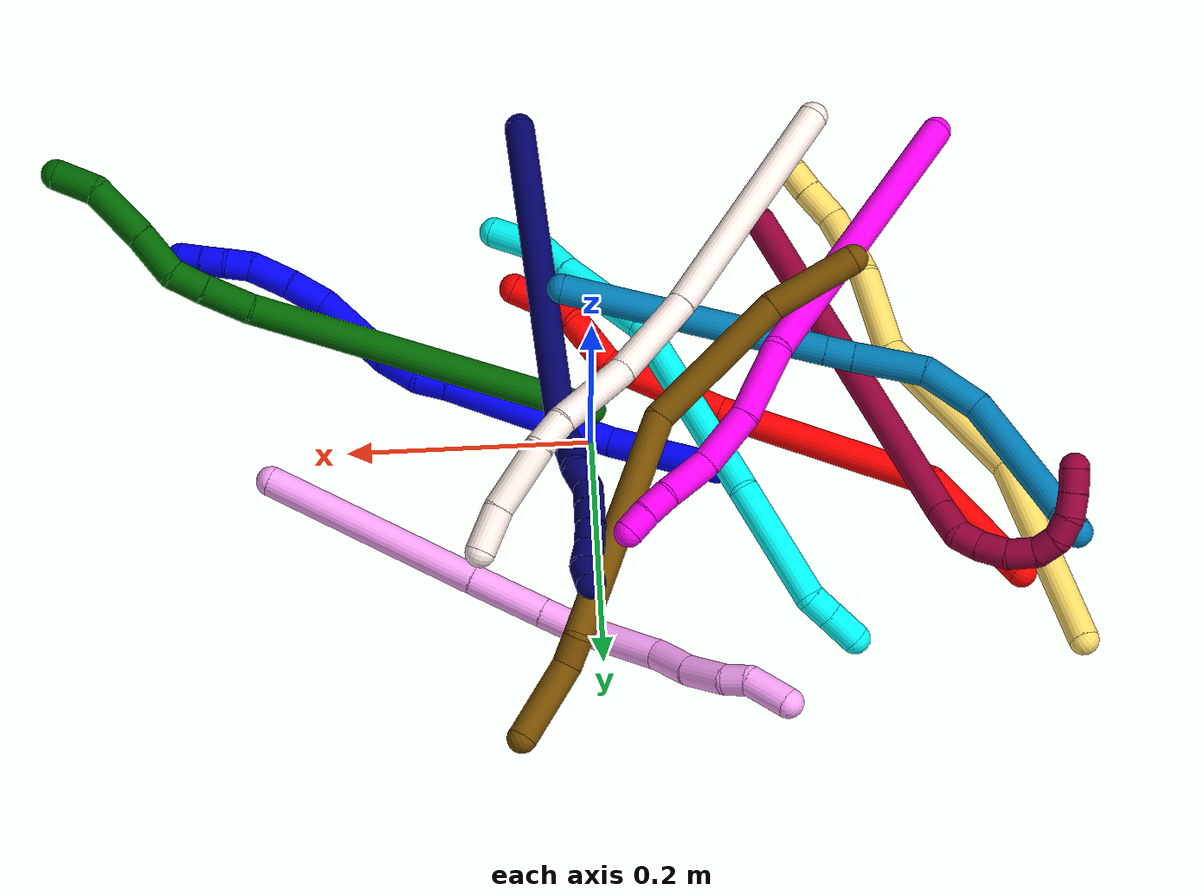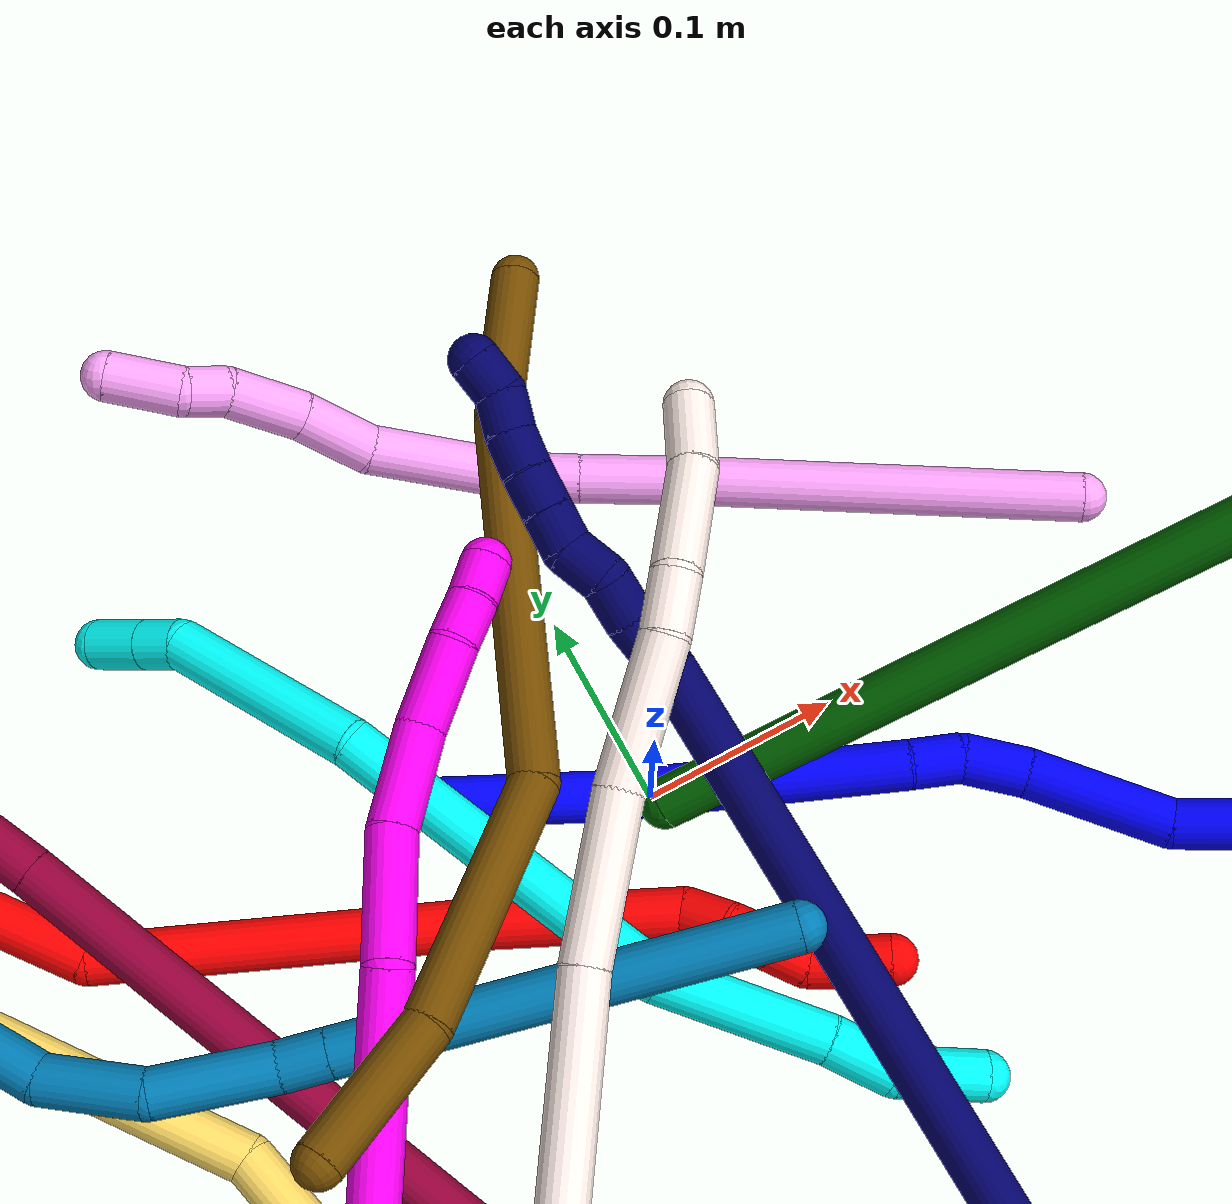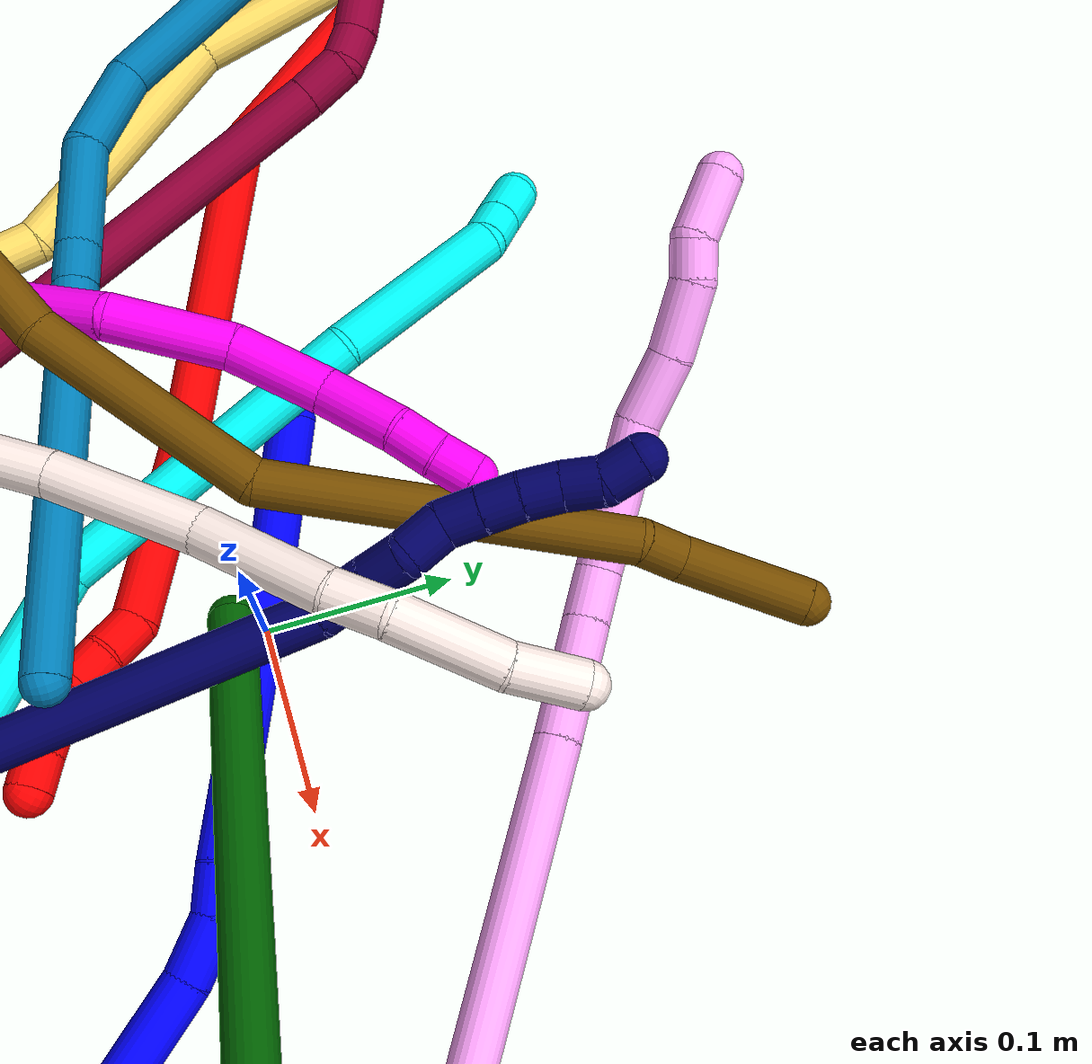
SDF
<sdf version="1.7">
 <world name="default">
  <plugin name="TubeGeneratorPlugin" filename="libtube_generator_plugin.so"/>
  <model name="photoneo_s_sensor">
   <static>1</static>
   <pose>0 0 2 1.57079 1.57079 3.14159</pose>
   <link name="link">
    <inertial><mass>0.1</mass></inertial>
    <sensor name="sensor" type="depth">
     <update_rate>30</update_rate>
     <camera>
      <horizontal_fov>1.22</horizontal_fov>
      <image><width>1920</width><height>1200</height><format>B8G8R8</format></image>
      <clip><near>0.1</near><far>4</far></clip>
      <depth_camera><output>points</output></depth_camera>
     </camera>
     <plugin name="camera_plugin" filename="libgazebo_ros_depth_camera.so">
      <baseline>0.2</baseline>
      <alwaysOn>1</alwaysOn>
      <updateRate>0.0</updateRate>
      <cameraName>camera_ir</cameraName>
      <imageTopicName>/camera/color/image_raw</imageTopicName>
      <cameraInfoTopicName>/camera/color/camera_info</cameraInfoTopicName>
      <depthImageTopicName>/camera/depth/image_raw</depthImageTopicName>
      <depthImageCameraInfoTopicName>/camera/depth/camera_info</depthImageCameraInfoTopicName>
      <pointCloudTopicName>/camera/depth/points</pointCloudTopicName>
      <frameName>fr_optical</frameName>
      <pointCloudCutoff>0.1</pointCloudCutoff>
      <pointCloudCutoffMax>2.0</pointCloudCutoffMax>
      <distortionK1>0</distortionK1>
      <distortionK2>0</distortionK2>
      <distortionK3>0</distortionK3>
      <distortionT1>0</distortionT1>
      <distortionT2>0</distortionT2>
      <CxPrime>0</CxPrime>
      <Cx>0</Cx>
      <Cy>0</Cy>
      <focalLength>0</focalLength>
      <hackBaseline>0</hackBaseline>
     </plugin>
    </sensor>
   </link>
  </model>
  <gravity>0 0 -9.8</gravity>
  <magnetic_field>6e-06 2.3e-05 -4.2e-05</magnetic_field>
  <atmosphere type="adiabatic"/>
  <physics name="default_physics" default="0" type="ode">
   <max_step_size>0.003</max_step_size>
   <real_time_factor>1</real_time_factor>
   <real_time_update_rate>1000</real_time_update_rate>
   <max_contacts>10000</max_contacts>
   <ode>
    <solver>
     <type>quick</type>
     <iters>100</iters>
     <sor>1.3</sor>
     <use_dynamic_moi_rescaling>0</use_dynamic_moi_rescaling>
    </solver>
    <constraints>
     <contact_max_correcting_vel>0</contact_max_correcting_vel>
     <contact_surface_layer>0.001</contact_surface_layer>
     <cfm>0</cfm>
     <erp>0.2</erp>
    </constraints>
   </ode>
  </physics>
  <scene><ambient>0.4 0.4 0.4 1</ambient><background>0.7 0.7 0.7 1</background><shadows>0</shadows></scene>
  <audio><device>default</device></audio>
  <spherical_coordinates>
   <surface_model>EARTH_WGS84</surface_model>
   <latitude_deg>0</latitude_deg>
   <longitude_deg>0</longitude_deg>
   <elevation>0</elevation>
   <heading_deg>0</heading_deg>
  </spherical_coordinates>
  <model name="bin">
   <static>1</static>
   <link name="bottom">
    <collision name="collision-bottom">
     <pose>0 0 -0.01 0 -0 0</pose>
     <geometry><box><size>0.8 0.6 0.02</size></box></geometry>
     <surface>
      <friction><ode><mu>100</mu><mu2>100</mu2></ode></friction>
      <contact><collide_bitmask>65535</collide_bitmask></contact>
     </surface>
    </collision>
   </link>
   <link name="west_wall">
    <collision name="collision-west_wall">
     <pose>-0.41 0 0.1 0 -0 0</pose>
     <geometry><box><size>0.02 0.6 0.2</size></box></geometry>
     <surface>
      <friction><ode><mu>100</mu><mu2>100</mu2></ode></friction>
      <contact><collide_bitmask>65535</collide_bitmask></contact>
     </surface>
    </collision>
   </link>
   <link name="east_wall">
    <collision name="collision-east_wall">
     <pose>0.41 0 0.1 0 -0 0</pose>
     <geometry><box><size>0.02 0.6 0.2</size></box></geometry>
     <surface>
      <friction><ode><mu>100</mu><mu2>100</mu2></ode></friction>
      <contact><collide_bitmask>65535</collide_bitmask></contact>
     </surface>
    </collision>
   </link>
   <link name="south_wall">
    <collision name="collision-south_wall">
     <pose>0 -0.31 0.1 0 -0 0</pose>
     <geometry><box><size>0.8 0.02 0.2</size></box></geometry>
     <surface>
      <friction><ode><mu>100</mu><mu2>100</mu2></ode></friction>
      <contact><collide_bitmask>65535</collide_bitmask></contact>
     </surface>
    </collision>
   </link>
   <link name="north_wall">
    <collision name="collision-north_wall">
     <pose>0 0.31 0.1 0 -0 0</pose>
     <geometry><box><size>0.8 0.02 0.2</size></box></geometry>
     <surface>
      <friction><ode><mu>100</mu><mu2>100</mu2></ode></friction>
      <contact><collide_bitmask>65535</collide_bitmask></contact>
     </surface>
    </collision>
   </link>
  </model>
  <model name="1">
   <static>0</static>
   <link name="1">
    <collision name="collision-cylinder-e_1_1_4">
     <pose>0.042112 -0.017157 -0.010216 2.10785 1.12803 1.67752</pose>
     <geometry><cylinder><radius>0.0125</radius><length>0.093213</length></cylinder></geometry>
     <surface>
      <friction><ode><mu>1.16</mu><mu2>1.16</mu2><slip1>0</slip1><slip2>0</slip2></ode></friction>
      <contact><ode><kp>1e+06</kp><kd>1</kd><max_vel>0</max_vel><min_depth>0.001</min_depth></ode></contact>
     </surface>
    </collision>
    <visual name="visual-cylinder-e_1_1_4">
     <pose>0.042112 -0.017157 -0.010216 2.10785 1.12803 1.67752</pose>
     <geometry><cylinder><radius>0.0125</radius><length>0.093213</length></cylinder></geometry>
     <material><ambient>0 0 1 1</ambient></material>
    </visual>
    <collision name="collision-cylinder-e_2_4_5">
     <pose>0.151645 -0.059025 -0.020907 1.59003 1.21942 1.23755</pose>
     <geometry><cylinder><radius>0.0125</radius><length>0.143616</length></cylinder></geometry>
     <surface>
      <friction><ode><mu>1.16</mu><mu2>1.16</mu2><slip1>0</slip1><slip2>0</slip2></ode></friction>
      <contact><ode><kp>1e+06</kp><kd>1</kd><max_vel>0</max_vel><min_depth>0.001</min_depth></ode></contact>
     </surface>
    </collision>
    <visual name="visual-cylinder-e_2_4_5">
     <pose>0.151645 -0.059025 -0.020907 1.59003 1.21942 1.23755</pose>
     <geometry><cylinder><radius>0.0125</radius><length>0.143616</length></cylinder></geometry>
     <material><ambient>0 0 1 1</ambient></material>
    </visual>
    <collision name="collision-cylinder-e_3_5_6">
     <pose>0.231171 -0.087609 -0.022873 1.93816 1.24044 1.61017</pose>
     <geometry><cylinder><radius>0.0125</radius><length>0.025594</length></cylinder></geometry>
     <surface>
      <friction><ode><mu>1.16</mu><mu2>1.16</mu2><slip1>0</slip1><slip2>0</slip2></ode></friction>
      <contact><ode><kp>1e+06</kp><kd>1</kd><max_vel>0</max_vel><min_depth>0.001</min_depth></ode></contact>
     </surface>
    </collision>
    <visual name="visual-cylinder-e_3_5_6">
     <pose>0.231171 -0.087609 -0.022873 1.93816 1.24044 1.61017</pose>
     <geometry><cylinder><radius>0.0125</radius><length>0.025594</length></cylinder></geometry>
     <material><ambient>0 0 1 1</ambient></material>
    </visual>
    <collision name="collision-cylinder-e_4_6_7">
     <pose>0.256211 -0.101572 -0.026519 1.78117 0.897541 1.0738</pose>
     <geometry><cylinder><radius>0.0125</radius><length>0.033091</length></cylinder></geometry>
     <surface>
      <friction><ode><mu>1.16</mu><mu2>1.16</mu2><slip1>0</slip1><slip2>0</slip2></ode></friction>
      <contact><ode><kp>1e+06</kp><kd>1</kd><max_vel>0</max_vel><min_depth>0.001</min_depth></ode></contact>
     </surface>
    </collision>
    <visual name="visual-cylinder-e_4_6_7">
     <pose>0.256211 -0.101572 -0.026519 1.78117 0.897541 1.0738</pose>
     <geometry><cylinder><radius>0.0125</radius><length>0.033091</length></cylinder></geometry>
     <material><ambient>0 0 1 1</ambient></material>
    </visual>
    <collision name="collision-cylinder-e_5_7_8">
     <pose>0.294826 -0.138255 -0.02867 1.57067 0.767923 0.767835</pose>
     <geometry><cylinder><radius>0.0125</radius><length>0.073938</length></cylinder></geometry>
     <surface>
      <friction><ode><mu>1.16</mu><mu2>1.16</mu2><slip1>0</slip1><slip2>0</slip2></ode></friction>
      <contact><ode><kp>1e+06</kp><kd>1</kd><max_vel>0</max_vel><min_depth>0.001</min_depth></ode></contact>
     </surface>
    </collision>
    <visual name="visual-cylinder-e_5_7_8">
     <pose>0.294826 -0.138255 -0.02867 1.57067 0.767923 0.767835</pose>
     <geometry><cylinder><radius>0.0125</radius><length>0.073938</length></cylinder></geometry>
     <material><ambient>0 0 1 1</ambient></material>
    </visual>
    <collision name="collision-cylinder-e_6_8_9">
     <pose>0.335014 -0.172377 -0.02642 1.2808 1.07453 0.835555</pose>
     <geometry><cylinder><radius>0.0125</radius><length>0.032997</length></cylinder></geometry>
     <surface>
      <friction><ode><mu>1.16</mu><mu2>1.16</mu2><slip1>0</slip1><slip2>0</slip2></ode></friction>
      <contact><ode><kp>1e+06</kp><kd>1</kd><max_vel>0</max_vel><min_depth>0.001</min_depth></ode></contact>
     </surface>
    </collision>
    <visual name="visual-cylinder-e_6_8_9">
     <pose>0.335014 -0.172377 -0.02642 1.2808 1.07453 0.835555</pose>
     <geometry><cylinder><radius>0.0125</radius><length>0.032997</length></cylinder></geometry>
     <material><ambient>0 0 1 1</ambient></material>
    </visual>
    <collision name="collision-cylinder-e_7_9_10">
     <pose>0.365826 -0.187626 -0.023607 1.49759 1.12743 1.06232</pose>
     <geometry><cylinder><radius>0.0125</radius><length>0.036097</length></cylinder></geometry>
     <surface>
      <friction><ode><mu>1.16</mu><mu2>1.16</mu2><slip1>0</slip1><slip2>0</slip2></ode></friction>
      <contact><ode><kp>1e+06</kp><kd>1</kd><max_vel>0</max_vel><min_depth>0.001</min_depth></ode></contact>
     </surface>
    </collision>
    <visual name="visual-cylinder-e_7_9_10">
     <pose>0.365826 -0.187626 -0.023607 1.49759 1.12743 1.06232</pose>
     <geometry><cylinder><radius>0.0125</radius><length>0.036097</length></cylinder></geometry>
     <material><ambient>0 0 1 1</ambient></material>
    </visual>
    <collision name="collision-cylinder-e_8_10_11">
     <pose>0.392533 -0.19674 -0.023564 1.92996 1.42882 1.79362</pose>
     <geometry><cylinder><radius>0.0125</radius><length>0.021018</length></cylinder></geometry>
     <surface>
      <friction><ode><mu>1.16</mu><mu2>1.16</mu2><slip1>0</slip1><slip2>0</slip2></ode></friction>
      <contact><ode><kp>1e+06</kp><kd>1</kd><max_vel>0</max_vel><min_depth>0.001</min_depth></ode></contact>
     </surface>
    </collision>
    <visual name="visual-cylinder-e_8_10_11">
     <pose>0.392533 -0.19674 -0.023564 1.92996 1.42882 1.79362</pose>
     <geometry><cylinder><radius>0.0125</radius><length>0.021018</length></cylinder></geometry>
     <material><ambient>0 0 1 1</ambient></material>
    </visual>
    <collision name="collision-cylinder-e_9_11_12">
     <pose>0.412448 -0.200584 -0.026494 2.347 1.22415 2.06409</pose>
     <geometry><cylinder><radius>0.0125</radius><length>0.020228</length></cylinder></geometry>
     <surface>
      <friction><ode><mu>1.16</mu><mu2>1.16</mu2><slip1>0</slip1><slip2>0</slip2></ode></friction>
      <contact><ode><kp>1e+06</kp><kd>1</kd><max_vel>0</max_vel><min_depth>0.001</min_depth></ode></contact>
     </surface>
    </collision>
    <visual name="visual-cylinder-e_9_11_12">
     <pose>0.412448 -0.200584 -0.026494 2.347 1.22415 2.06409</pose>
     <geometry><cylinder><radius>0.0125</radius><length>0.020228</length></cylinder></geometry>
     <material><ambient>0 0 1 1</ambient></material>
    </visual>
    <collision name="collision-cylinder-e_10_12_2">
     <pose>0.431204 -0.20597 -0.031739 2.3395 1.15499 1.98778</pose>
     <geometry><cylinder><radius>0.0125</radius><length>0.020209</length></cylinder></geometry>
     <surface>
      <friction><ode><mu>1.16</mu><mu2>1.16</mu2><slip1>0</slip1><slip2>0</slip2></ode></friction>
      <contact><ode><kp>1e+06</kp><kd>1</kd><max_vel>0</max_vel><min_depth>0.001</min_depth></ode></contact>
     </surface>
    </collision>
    <visual name="visual-cylinder-e_10_12_2">
     <pose>0.431204 -0.20597 -0.031739 2.3395 1.15499 1.98778</pose>
     <geometry><cylinder><radius>0.0125</radius><length>0.020209</length></cylinder></geometry>
     <material><ambient>0 0 1 1</ambient></material>
    </visual>
    <collision name="collision-sphere-2">
     <pose>0.440448 -0.208904 -0.034576 0 -0 0</pose>
     <geometry><sphere><radius>0.0125</radius></sphere></geometry>
     <surface>
      <friction><ode><mu>1.16</mu><mu2>1.16</mu2><slip1>0</slip1><slip2>0</slip2></ode></friction>
      <contact><ode><kp>1e+06</kp><kd>1</kd><max_vel>0</max_vel><min_depth>0.001</min_depth></ode></contact>
     </surface>
    </collision>
    <visual name="visual-sphere-2">
     <pose>0.440448 -0.208904 -0.034576 0 -0 0</pose>
     <geometry><sphere><radius>0.0125</radius></sphere></geometry>
     <material><ambient>0 0 1 1</ambient></material>
    </visual>
    <collision name="collision-sphere-12">
     <pose>0.42196 -0.203036 -0.028901 0 -0 0</pose>
     <geometry><sphere><radius>0.0125</radius></sphere></geometry>
     <surface>
      <friction><ode><mu>1.16</mu><mu2>1.16</mu2><slip1>0</slip1><slip2>0</slip2></ode></friction>
      <contact><ode><kp>1e+06</kp><kd>1</kd><max_vel>0</max_vel><min_depth>0.001</min_depth></ode></contact>
     </surface>
    </collision>
    <visual name="visual-sphere-12">
     <pose>0.42196 -0.203036 -0.028901 0 -0 0</pose>
     <geometry><sphere><radius>0.0125</radius></sphere></geometry>
     <material><ambient>0 0 1 1</ambient></material>
    </visual>
    <collision name="collision-sphere-11">
     <pose>0.402936 -0.198132 -0.024087 0 -0 0</pose>
     <geometry><sphere><radius>0.0125</radius></sphere></geometry>
     <surface>
      <friction><ode><mu>1.16</mu><mu2>1.16</mu2><slip1>0</slip1><slip2>0</slip2></ode></friction>
      <contact><ode><kp>1e+06</kp><kd>1</kd><max_vel>0</max_vel><min_depth>0.001</min_depth></ode></contact>
     </surface>
    </collision>
    <visual name="visual-sphere-11">
     <pose>0.402936 -0.198132 -0.024087 0 -0 0</pose>
     <geometry><sphere><radius>0.0125</radius></sphere></geometry>
     <material><ambient>0 0 1 1</ambient></material>
    </visual>
    <collision name="collision-sphere-10">
     <pose>0.38213 -0.195348 -0.023041 0 -0 0</pose>
     <geometry><sphere><radius>0.0125</radius></sphere></geometry>
     <surface>
      <friction><ode><mu>1.16</mu><mu2>1.16</mu2><slip1>0</slip1><slip2>0</slip2></ode></friction>
      <contact><ode><kp>1e+06</kp><kd>1</kd><max_vel>0</max_vel><min_depth>0.001</min_depth></ode></contact>
     </surface>
    </collision>
    <visual name="visual-sphere-10">
     <pose>0.38213 -0.195348 -0.023041 0 -0 0</pose>
     <geometry><sphere><radius>0.0125</radius></sphere></geometry>
     <material><ambient>0 0 1 1</ambient></material>
    </visual>
    <collision name="collision-sphere-9">
     <pose>0.349522 -0.179904 -0.024174 0 -0 0</pose>
     <geometry><sphere><radius>0.0125</radius></sphere></geometry>
     <surface>
      <friction><ode><mu>1.16</mu><mu2>1.16</mu2><slip1>0</slip1><slip2>0</slip2></ode></friction>
      <contact><ode><kp>1e+06</kp><kd>1</kd><max_vel>0</max_vel><min_depth>0.001</min_depth></ode></contact>
     </surface>
    </collision>
    <visual name="visual-sphere-9">
     <pose>0.349522 -0.179904 -0.024174 0 -0 0</pose>
     <geometry><sphere><radius>0.0125</radius></sphere></geometry>
     <material><ambient>0 0 1 1</ambient></material>
    </visual>
    <collision name="collision-sphere-4">
     <pose>0.084225 -0.034314 -0.020432 0 -0 0</pose>
     <geometry><sphere><radius>0.0125</radius></sphere></geometry>
     <surface>
      <friction><ode><mu>1.16</mu><mu2>1.16</mu2><slip1>0</slip1><slip2>0</slip2></ode></friction>
      <contact><ode><kp>1e+06</kp><kd>1</kd><max_vel>0</max_vel><min_depth>0.001</min_depth></ode></contact>
     </surface>
    </collision>
    <visual name="visual-sphere-4">
     <pose>0.084225 -0.034314 -0.020432 0 -0 0</pose>
     <geometry><sphere><radius>0.0125</radius></sphere></geometry>
     <material><ambient>0 0 1 1</ambient></material>
    </visual>
    <collision name="collision-sphere-1">
     <geometry><sphere><radius>0.0125</radius></sphere></geometry>
     <surface>
      <friction><ode><mu>1.16</mu><mu2>1.16</mu2><slip1>0</slip1><slip2>0</slip2></ode></friction>
      <contact><ode><kp>1e+06</kp><kd>1</kd><max_vel>0</max_vel><min_depth>0.001</min_depth></ode></contact>
     </surface>
    </collision>
    <visual name="visual-sphere-1">
     <geometry><sphere><radius>0.0125</radius></sphere></geometry>
     <material><ambient>0 0 1 1</ambient></material>
    </visual>
    <collision name="collision-sphere-8">
     <pose>0.320506 -0.164849 -0.028666 0 -0 0</pose>
     <geometry><sphere><radius>0.0125</radius></sphere></geometry>
     <surface>
      <friction><ode><mu>1.16</mu><mu2>1.16</mu2><slip1>0</slip1><slip2>0</slip2></ode></friction>
      <contact><ode><kp>1e+06</kp><kd>1</kd><max_vel>0</max_vel><min_depth>0.001</min_depth></ode></contact>
     </surface>
    </collision>
    <visual name="visual-sphere-8">
     <pose>0.320506 -0.164849 -0.028666 0 -0 0</pose>
     <geometry><sphere><radius>0.0125</radius></sphere></geometry>
     <material><ambient>0 0 1 1</ambient></material>
    </visual>
    <collision name="collision-sphere-5">
     <pose>0.219066 -0.083735 -0.021382 0 -0 0</pose>
     <geometry><sphere><radius>0.0125</radius></sphere></geometry>
     <surface>
      <friction><ode><mu>1.16</mu><mu2>1.16</mu2><slip1>0</slip1><slip2>0</slip2></ode></friction>
      <contact><ode><kp>1e+06</kp><kd>1</kd><max_vel>0</max_vel><min_depth>0.001</min_depth></ode></contact>
     </surface>
    </collision>
    <visual name="visual-sphere-5">
     <pose>0.219066 -0.083735 -0.021382 0 -0 0</pose>
     <geometry><sphere><radius>0.0125</radius></sphere></geometry>
     <material><ambient>0 0 1 1</ambient></material>
    </visual>
    <collision name="collision-sphere-6">
     <pose>0.243276 -0.091483 -0.024364 0 -0 0</pose>
     <geometry><sphere><radius>0.0125</radius></sphere></geometry>
     <surface>
      <friction><ode><mu>1.16</mu><mu2>1.16</mu2><slip1>0</slip1><slip2>0</slip2></ode></friction>
      <contact><ode><kp>1e+06</kp><kd>1</kd><max_vel>0</max_vel><min_depth>0.001</min_depth></ode></contact>
     </surface>
    </collision>
    <visual name="visual-sphere-6">
     <pose>0.243276 -0.091483 -0.024364 0 -0 0</pose>
     <geometry><sphere><radius>0.0125</radius></sphere></geometry>
     <material><ambient>0 0 1 1</ambient></material>
    </visual>
    <collision name="collision-sphere-7">
     <pose>0.269146 -0.111662 -0.028673 0 -0 0</pose>
     <geometry><sphere><radius>0.0125</radius></sphere></geometry>
     <surface>
      <friction><ode><mu>1.16</mu><mu2>1.16</mu2><slip1>0</slip1><slip2>0</slip2></ode></friction>
      <contact><ode><kp>1e+06</kp><kd>1</kd><max_vel>0</max_vel><min_depth>0.001</min_depth></ode></contact>
     </surface>
    </collision>
    <visual name="visual-sphere-7">
     <pose>0.269146 -0.111662 -0.028673 0 -0 0</pose>
     <geometry><sphere><radius>0.0125</radius></sphere></geometry>
     <material><ambient>0 0 1 1</ambient></material>
    </visual>
    <inertial>
     <pose>0.222929 -0.101435 -0.021868 0 -0 0</pose>
     <mass>0.5</mass>
     <inertia><ixx>0.00022</ixx><ixy>0</ixy><ixz>0</ixz><iyy>0.000438</iyy><iyz>0</iyz><izz>-0.0002</izz></inertia>
    </inertial>
   </link>
   <pose>-0.100846 0.042606 0.02762 0.095279 -0.087711 -0.051729</pose>
  </model>
  <model name="2">
   <static>0</static>
   <link name="2">
    <collision name="collision-cylinder-e_1_1_4">
     <pose>0.017048 -0.050882 0.011841 1.34214 0.315436 0.251225</pose>
     <geometry><cylinder><radius>0.0125</radius><length>0.109906</length></cylinder></geometry>
     <surface>
      <friction><ode><mu>1.16</mu><mu2>1.16</mu2><slip1>0</slip1><slip2>0</slip2></ode></friction>
      <contact><ode><kp>1e+06</kp><kd>1</kd><max_vel>0</max_vel><min_depth>0.001</min_depth></ode></contact>
     </surface>
    </collision>
    <visual name="visual-cylinder-e_1_1_4">
     <pose>0.017048 -0.050882 0.011841 1.34214 0.315436 0.251225</pose>
     <geometry><cylinder><radius>0.0125</radius><length>0.109906</length></cylinder></geometry>
     <material><ambient>1 0 0 1</ambient></material>
    </visual>
    <collision name="collision-cylinder-e_2_4_5">
     <pose>0.087703 -0.174346 0.006865 1.79849 0.623694 0.77065</pose>
     <geometry><cylinder><radius>0.0125</radius><length>0.183571</length></cylinder></geometry>
     <surface>
      <friction><ode><mu>1.16</mu><mu2>1.16</mu2><slip1>0</slip1><slip2>0</slip2></ode></friction>
      <contact><ode><kp>1e+06</kp><kd>1</kd><max_vel>0</max_vel><min_depth>0.001</min_depth></ode></contact>
     </surface>
    </collision>
    <visual name="visual-cylinder-e_2_4_5">
     <pose>0.087703 -0.174346 0.006865 1.79849 0.623694 0.77065</pose>
     <geometry><cylinder><radius>0.0125</radius><length>0.183571</length></cylinder></geometry>
     <material><ambient>1 0 0 1</ambient></material>
    </visual>
    <collision name="collision-cylinder-e_3_5_6">
     <pose>0.173005 -0.286893 -0.014467 1.68328 0.667442 0.740335</pose>
     <geometry><cylinder><radius>0.0125</radius><length>0.102416</length></cylinder></geometry>
     <surface>
      <friction><ode><mu>1.16</mu><mu2>1.16</mu2><slip1>0</slip1><slip2>0</slip2></ode></friction>
      <contact><ode><kp>1e+06</kp><kd>1</kd><max_vel>0</max_vel><min_depth>0.001</min_depth></ode></contact>
     </surface>
    </collision>
    <visual name="visual-cylinder-e_3_5_6">
     <pose>0.173005 -0.286893 -0.014467 1.68328 0.667442 0.740335</pose>
     <geometry><cylinder><radius>0.0125</radius><length>0.102416</length></cylinder></geometry>
     <material><ambient>1 0 0 1</ambient></material>
    </visual>
    <collision name="collision-cylinder-e_4_6_7">
     <pose>0.211059 -0.335785 -0.014242 1.08272 0.561437 0.343324</pose>
     <geometry><cylinder><radius>0.0125</radius><length>0.023881</length></cylinder></geometry>
     <surface>
      <friction><ode><mu>1.16</mu><mu2>1.16</mu2><slip1>0</slip1><slip2>0</slip2></ode></friction>
      <contact><ode><kp>1e+06</kp><kd>1</kd><max_vel>0</max_vel><min_depth>0.001</min_depth></ode></contact>
     </surface>
    </collision>
    <visual name="visual-cylinder-e_4_6_7">
     <pose>0.211059 -0.335785 -0.014242 1.08272 0.561437 0.343324</pose>
     <geometry><cylinder><radius>0.0125</radius><length>0.023881</length></cylinder></geometry>
     <material><ambient>1 0 0 1</ambient></material>
    </visual>
    <collision name="collision-cylinder-e_5_7_8">
     <pose>0.221375 -0.353373 -0.006142 1.20067 0.402829 0.277778</pose>
     <geometry><cylinder><radius>0.0125</radius><length>0.020198</length></cylinder></geometry>
     <surface>
      <friction><ode><mu>1.16</mu><mu2>1.16</mu2><slip1>0</slip1><slip2>0</slip2></ode></friction>
      <contact><ode><kp>1e+06</kp><kd>1</kd><max_vel>0</max_vel><min_depth>0.001</min_depth></ode></contact>
     </surface>
    </collision>
    <visual name="visual-cylinder-e_5_7_8">
     <pose>0.221375 -0.353373 -0.006142 1.20067 0.402829 0.277778</pose>
     <geometry><cylinder><radius>0.0125</radius><length>0.020198</length></cylinder></geometry>
     <material><ambient>1 0 0 1</ambient></material>
    </visual>
    <collision name="collision-cylinder-e_6_8_9">
     <pose>0.226831 -0.371916 -0.002311 1.52324 0.150207 0.143253</pose>
     <geometry><cylinder><radius>0.0125</radius><length>0.02001</length></cylinder></geometry>
     <surface>
      <friction><ode><mu>1.16</mu><mu2>1.16</mu2><slip1>0</slip1><slip2>0</slip2></ode></friction>
      <contact><ode><kp>1e+06</kp><kd>1</kd><max_vel>0</max_vel><min_depth>0.001</min_depth></ode></contact>
     </surface>
    </collision>
    <visual name="visual-cylinder-e_6_8_9">
     <pose>0.226831 -0.371916 -0.002311 1.52324 0.150207 0.143253</pose>
     <geometry><cylinder><radius>0.0125</radius><length>0.02001</length></cylinder></geometry>
     <material><ambient>1 0 0 1</ambient></material>
    </visual>
    <collision name="collision-cylinder-e_7_9_10">
     <pose>0.234152 -0.38991 -0.002439 1.64436 0.621316 0.665472</pose>
     <geometry><cylinder><radius>0.0125</radius><length>0.020008</length></cylinder></geometry>
     <surface>
      <friction><ode><mu>1.16</mu><mu2>1.16</mu2><slip1>0</slip1><slip2>0</slip2></ode></friction>
      <contact><ode><kp>1e+06</kp><kd>1</kd><max_vel>0</max_vel><min_depth>0.001</min_depth></ode></contact>
     </surface>
    </collision>
    <visual name="visual-cylinder-e_7_9_10">
     <pose>0.234152 -0.38991 -0.002439 1.64436 0.621316 0.665472</pose>
     <geometry><cylinder><radius>0.0125</radius><length>0.020008</length></cylinder></geometry>
     <material><ambient>1 0 0 1</ambient></material>
    </visual>
    <collision name="collision-cylinder-e_8_10_2">
     <pose>0.246251 -0.405777 -0.003805 1.66953 0.677973 0.742411</pose>
     <geometry><cylinder><radius>0.0125</radius><length>0.02001</length></cylinder></geometry>
     <surface>
      <friction><ode><mu>1.16</mu><mu2>1.16</mu2><slip1>0</slip1><slip2>0</slip2></ode></friction>
      <contact><ode><kp>1e+06</kp><kd>1</kd><max_vel>0</max_vel><min_depth>0.001</min_depth></ode></contact>
     </surface>
    </collision>
    <visual name="visual-cylinder-e_8_10_2">
     <pose>0.246251 -0.405777 -0.003805 1.66953 0.677973 0.742411</pose>
     <geometry><cylinder><radius>0.0125</radius><length>0.02001</length></cylinder></geometry>
     <material><ambient>1 0 0 1</ambient></material>
    </visual>
    <collision name="collision-sphere-2">
     <pose>0.252526 -0.413531 -0.004573 0 -0 0</pose>
     <geometry><sphere><radius>0.0125</radius></sphere></geometry>
     <surface>
      <friction><ode><mu>1.16</mu><mu2>1.16</mu2><slip1>0</slip1><slip2>0</slip2></ode></friction>
      <contact><ode><kp>1e+06</kp><kd>1</kd><max_vel>0</max_vel><min_depth>0.001</min_depth></ode></contact>
     </surface>
    </collision>
    <visual name="visual-sphere-2">
     <pose>0.252526 -0.413531 -0.004573 0 -0 0</pose>
     <geometry><sphere><radius>0.0125</radius></sphere></geometry>
     <material><ambient>1 0 0 1</ambient></material>
    </visual>
    <collision name="collision-sphere-10">
     <pose>0.239975 -0.398022 -0.003036 0 -0 0</pose>
     <geometry><sphere><radius>0.0125</radius></sphere></geometry>
     <surface>
      <friction><ode><mu>1.16</mu><mu2>1.16</mu2><slip1>0</slip1><slip2>0</slip2></ode></friction>
      <contact><ode><kp>1e+06</kp><kd>1</kd><max_vel>0</max_vel><min_depth>0.001</min_depth></ode></contact>
     </surface>
    </collision>
    <visual name="visual-sphere-10">
     <pose>0.239975 -0.398022 -0.003036 0 -0 0</pose>
     <geometry><sphere><radius>0.0125</radius></sphere></geometry>
     <material><ambient>1 0 0 1</ambient></material>
    </visual>
    <collision name="collision-sphere-9">
     <pose>0.228329 -0.381797 -0.001841 0 -0 0</pose>
     <geometry><sphere><radius>0.0125</radius></sphere></geometry>
     <surface>
      <friction><ode><mu>1.16</mu><mu2>1.16</mu2><slip1>0</slip1><slip2>0</slip2></ode></friction>
      <contact><ode><kp>1e+06</kp><kd>1</kd><max_vel>0</max_vel><min_depth>0.001</min_depth></ode></contact>
     </surface>
    </collision>
    <visual name="visual-sphere-9">
     <pose>0.228329 -0.381797 -0.001841 0 -0 0</pose>
     <geometry><sphere><radius>0.0125</radius></sphere></geometry>
     <material><ambient>1 0 0 1</ambient></material>
    </visual>
    <collision name="collision-sphere-4">
     <pose>0.034096 -0.101764 0.023683 0 -0 0</pose>
     <geometry><sphere><radius>0.0125</radius></sphere></geometry>
     <surface>
      <friction><ode><mu>1.16</mu><mu2>1.16</mu2><slip1>0</slip1><slip2>0</slip2></ode></friction>
      <contact><ode><kp>1e+06</kp><kd>1</kd><max_vel>0</max_vel><min_depth>0.001</min_depth></ode></contact>
     </surface>
    </collision>
    <visual name="visual-sphere-4">
     <pose>0.034096 -0.101764 0.023683 0 -0 0</pose>
     <geometry><sphere><radius>0.0125</radius></sphere></geometry>
     <material><ambient>1 0 0 1</ambient></material>
    </visual>
    <collision name="collision-sphere-1">
     <geometry><sphere><radius>0.0125</radius></sphere></geometry>
     <surface>
      <friction><ode><mu>1.16</mu><mu2>1.16</mu2><slip1>0</slip1><slip2>0</slip2></ode></friction>
      <contact><ode><kp>1e+06</kp><kd>1</kd><max_vel>0</max_vel><min_depth>0.001</min_depth></ode></contact>
     </surface>
    </collision>
    <visual name="visual-sphere-1">
     <geometry><sphere><radius>0.0125</radius></sphere></geometry>
     <material><ambient>1 0 0 1</ambient></material>
    </visual>
    <collision name="collision-sphere-8">
     <pose>0.225334 -0.362035 -0.002781 0 -0 0</pose>
     <geometry><sphere><radius>0.0125</radius></sphere></geometry>
     <surface>
      <friction><ode><mu>1.16</mu><mu2>1.16</mu2><slip1>0</slip1><slip2>0</slip2></ode></friction>
      <contact><ode><kp>1e+06</kp><kd>1</kd><max_vel>0</max_vel><min_depth>0.001</min_depth></ode></contact>
     </surface>
    </collision>
    <visual name="visual-sphere-8">
     <pose>0.225334 -0.362035 -0.002781 0 -0 0</pose>
     <geometry><sphere><radius>0.0125</radius></sphere></geometry>
     <material><ambient>1 0 0 1</ambient></material>
    </visual>
    <collision name="collision-sphere-5">
     <pose>0.141309 -0.246928 -0.009953 0 -0 0</pose>
     <geometry><sphere><radius>0.0125</radius></sphere></geometry>
     <surface>
      <friction><ode><mu>1.16</mu><mu2>1.16</mu2><slip1>0</slip1><slip2>0</slip2></ode></friction>
      <contact><ode><kp>1e+06</kp><kd>1</kd><max_vel>0</max_vel><min_depth>0.001</min_depth></ode></contact>
     </surface>
    </collision>
    <visual name="visual-sphere-5">
     <pose>0.141309 -0.246928 -0.009953 0 -0 0</pose>
     <geometry><sphere><radius>0.0125</radius></sphere></geometry>
     <material><ambient>1 0 0 1</ambient></material>
    </visual>
    <collision name="collision-sphere-6">
     <pose>0.204702 -0.326858 -0.018982 0 -0 0</pose>
     <geometry><sphere><radius>0.0125</radius></sphere></geometry>
     <surface>
      <friction><ode><mu>1.16</mu><mu2>1.16</mu2><slip1>0</slip1><slip2>0</slip2></ode></friction>
      <contact><ode><kp>1e+06</kp><kd>1</kd><max_vel>0</max_vel><min_depth>0.001</min_depth></ode></contact>
     </surface>
    </collision>
    <visual name="visual-sphere-6">
     <pose>0.204702 -0.326858 -0.018982 0 -0 0</pose>
     <geometry><sphere><radius>0.0125</radius></sphere></geometry>
     <material><ambient>1 0 0 1</ambient></material>
    </visual>
    <collision name="collision-sphere-7">
     <pose>0.217416 -0.344712 -0.009503 0 -0 0</pose>
     <geometry><sphere><radius>0.0125</radius></sphere></geometry>
     <surface>
      <friction><ode><mu>1.16</mu><mu2>1.16</mu2><slip1>0</slip1><slip2>0</slip2></ode></friction>
      <contact><ode><kp>1e+06</kp><kd>1</kd><max_vel>0</max_vel><min_depth>0.001</min_depth></ode></contact>
     </surface>
    </collision>
    <visual name="visual-sphere-7">
     <pose>0.217416 -0.344712 -0.009503 0 -0 0</pose>
     <geometry><sphere><radius>0.0125</radius></sphere></geometry>
     <material><ambient>1 0 0 1</ambient></material>
    </visual>
    <inertial>
     <pose>0.118709 -0.210997 0.000889 0 -0 0</pose>
     <mass>0.5</mass>
     <inertia>
      <ixx>0.000865</ixx>
      <ixy>0</ixy>
      <ixz>0</ixz>
      <iyy>0.000533</iyy>
      <iyz>0</iyz>
      <izz>0.000196</izz>
     </inertia>
    </inertial>
   </link>
   <pose>-0.343339 0.142122 0.01142 0.560754 -0.786234 0.203623</pose>
  </model>
  <model name="3">
   <static>0</static>
   <link name="3">
    <collision name="collision-cylinder-e_1_1_4">
     <pose>0.005304 0.018757 0.009859 -1.08686 0.245249 -0.148628</pose>
     <geometry><cylinder><radius>0.0125</radius><length>0.043688</length></cylinder></geometry>
     <surface>
      <friction><ode><mu>1.16</mu><mu2>1.16</mu2><slip1>0</slip1><slip2>0</slip2></ode></friction>
      <contact><ode><kp>1e+06</kp><kd>1</kd><max_vel>0</max_vel><min_depth>0.001</min_depth></ode></contact>
     </surface>
    </collision>
    <visual name="visual-cylinder-e_1_1_4">
     <pose>0.005304 0.018757 0.009859 -1.08686 0.245249 -0.148628</pose>
     <geometry><cylinder><radius>0.0125</radius><length>0.043688</length></cylinder></geometry>
     <material><ambient>0.003922 1 0.996078 1</ambient></material>
    </visual>
    <collision name="collision-cylinder-e_2_4_5">
     <pose>0.008256 0.051518 0.029446 -0.963685 -0.137054 0.071755</pose>
     <geometry><cylinder><radius>0.0125</radius><length>0.034426</length></cylinder></geometry>
     <surface>
      <friction><ode><mu>1.16</mu><mu2>1.16</mu2><slip1>0</slip1><slip2>0</slip2></ode></friction>
      <contact><ode><kp>1e+06</kp><kd>1</kd><max_vel>0</max_vel><min_depth>0.001</min_depth></ode></contact>
     </surface>
    </collision>
    <visual name="visual-cylinder-e_2_4_5">
     <pose>0.008256 0.051518 0.029446 -0.963685 -0.137054 0.071755</pose>
     <geometry><cylinder><radius>0.0125</radius><length>0.034426</length></cylinder></geometry>
     <material><ambient>0.003922 1 0.996078 1</ambient></material>
    </visual>
    <collision name="collision-cylinder-e_3_5_6">
     <pose>0.004808 0.100951 0.063854 -0.96234 -0.025382 0.013253</pose>
     <geometry><cylinder><radius>0.0125</radius><length>0.08638</length></cylinder></geometry>
     <surface>
      <friction><ode><mu>1.16</mu><mu2>1.16</mu2><slip1>0</slip1><slip2>0</slip2></ode></friction>
      <contact><ode><kp>1e+06</kp><kd>1</kd><max_vel>0</max_vel><min_depth>0.001</min_depth></ode></contact>
     </surface>
    </collision>
    <visual name="visual-cylinder-e_3_5_6">
     <pose>0.004808 0.100951 0.063854 -0.96234 -0.025382 0.013253</pose>
     <geometry><cylinder><radius>0.0125</radius><length>0.08638</length></cylinder></geometry>
     <material><ambient>0.003922 1 0.996078 1</ambient></material>
    </visual>
    <collision name="collision-cylinder-e_4_6_7">
     <pose>-0.024306 0.196929 0.149487 -0.782085 -0.315227 0.13086</pose>
     <geometry><cylinder><radius>0.0125</radius><length>0.18074</length></cylinder></geometry>
     <surface>
      <friction><ode><mu>1.16</mu><mu2>1.16</mu2><slip1>0</slip1><slip2>0</slip2></ode></friction>
      <contact><ode><kp>1e+06</kp><kd>1</kd><max_vel>0</max_vel><min_depth>0.001</min_depth></ode></contact>
     </surface>
    </collision>
    <visual name="visual-cylinder-e_4_6_7">
     <pose>-0.024306 0.196929 0.149487 -0.782085 -0.315227 0.13086</pose>
     <geometry><cylinder><radius>0.0125</radius><length>0.18074</length></cylinder></geometry>
     <material><ambient>0.003922 1 0.996078 1</ambient></material>
    </visual>
    <collision name="collision-cylinder-e_5_7_8">
     <pose>-0.060224 0.283638 0.254953 -0.531296 -0.151846 0.041388</pose>
     <geometry><cylinder><radius>0.0125</radius><length>0.104462</length></cylinder></geometry>
     <surface>
      <friction><ode><mu>1.16</mu><mu2>1.16</mu2><slip1>0</slip1><slip2>0</slip2></ode></friction>
      <contact><ode><kp>1e+06</kp><kd>1</kd><max_vel>0</max_vel><min_depth>0.001</min_depth></ode></contact>
     </surface>
    </collision>
    <visual name="visual-cylinder-e_5_7_8">
     <pose>-0.060224 0.283638 0.254953 -0.531296 -0.151846 0.041388</pose>
     <geometry><cylinder><radius>0.0125</radius><length>0.104462</length></cylinder></geometry>
     <material><ambient>0.003922 1 0.996078 1</ambient></material>
    </visual>
    <collision name="collision-cylinder-e_6_8_9">
     <pose>-0.064999 0.313647 0.308715 -0.394474 0.302475 -0.060891</pose>
     <geometry><cylinder><radius>0.0125</radius><length>0.020989</length></cylinder></geometry>
     <surface>
      <friction><ode><mu>1.16</mu><mu2>1.16</mu2><slip1>0</slip1><slip2>0</slip2></ode></friction>
      <contact><ode><kp>1e+06</kp><kd>1</kd><max_vel>0</max_vel><min_depth>0.001</min_depth></ode></contact>
     </surface>
    </collision>
    <visual name="visual-cylinder-e_6_8_9">
     <pose>-0.064999 0.313647 0.308715 -0.394474 0.302475 -0.060891</pose>
     <geometry><cylinder><radius>0.0125</radius><length>0.020989</length></cylinder></geometry>
     <material><ambient>0.003922 1 0.996078 1</ambient></material>
    </visual>
    <collision name="collision-cylinder-e_7_9_2">
     <pose>-0.057597 0.322714 0.330977 -0.381259 0.296031 -0.057531</pose>
     <geometry><cylinder><radius>0.0125</radius><length>0.029315</length></cylinder></geometry>
     <surface>
      <friction><ode><mu>1.16</mu><mu2>1.16</mu2><slip1>0</slip1><slip2>0</slip2></ode></friction>
      <contact><ode><kp>1e+06</kp><kd>1</kd><max_vel>0</max_vel><min_depth>0.001</min_depth></ode></contact>
     </surface>
    </collision>
    <visual name="visual-cylinder-e_7_9_2">
     <pose>-0.057597 0.322714 0.330977 -0.381259 0.296031 -0.057531</pose>
     <geometry><cylinder><radius>0.0125</radius><length>0.029315</length></cylinder></geometry>
     <material><ambient>0.003922 1 0.996078 1</ambient></material>
    </visual>
    <collision name="collision-sphere-2">
     <pose>-0.053321 0.32793 0.34399 0 -0 0</pose>
     <geometry><sphere><radius>0.0125</radius></sphere></geometry>
     <surface>
      <friction><ode><mu>1.16</mu><mu2>1.16</mu2><slip1>0</slip1><slip2>0</slip2></ode></friction>
      <contact><ode><kp>1e+06</kp><kd>1</kd><max_vel>0</max_vel><min_depth>0.001</min_depth></ode></contact>
     </surface>
    </collision>
    <visual name="visual-sphere-2">
     <pose>-0.053321 0.32793 0.34399 0 -0 0</pose>
     <geometry><sphere><radius>0.0125</radius></sphere></geometry>
     <material><ambient>0.003922 1 0.996078 1</ambient></material>
    </visual>
    <collision name="collision-sphere-9">
     <pose>-0.061873 0.317497 0.317964 0 -0 0</pose>
     <geometry><sphere><radius>0.0125</radius></sphere></geometry>
     <surface>
      <friction><ode><mu>1.16</mu><mu2>1.16</mu2><slip1>0</slip1><slip2>0</slip2></ode></friction>
      <contact><ode><kp>1e+06</kp><kd>1</kd><max_vel>0</max_vel><min_depth>0.001</min_depth></ode></contact>
     </surface>
    </collision>
    <visual name="visual-sphere-9">
     <pose>-0.061873 0.317497 0.317964 0 -0 0</pose>
     <geometry><sphere><radius>0.0125</radius></sphere></geometry>
     <material><ambient>0.003922 1 0.996078 1</ambient></material>
    </visual>
    <collision name="collision-sphere-4">
     <pose>0.010607 0.037514 0.019718 0 -0 0</pose>
     <geometry><sphere><radius>0.0125</radius></sphere></geometry>
     <surface>
      <friction><ode><mu>1.16</mu><mu2>1.16</mu2><slip1>0</slip1><slip2>0</slip2></ode></friction>
      <contact><ode><kp>1e+06</kp><kd>1</kd><max_vel>0</max_vel><min_depth>0.001</min_depth></ode></contact>
     </surface>
    </collision>
    <visual name="visual-sphere-4">
     <pose>0.010607 0.037514 0.019718 0 -0 0</pose>
     <geometry><sphere><radius>0.0125</radius></sphere></geometry>
     <material><ambient>0.003922 1 0.996078 1</ambient></material>
    </visual>
    <collision name="collision-sphere-1">
     <geometry><sphere><radius>0.0125</radius></sphere></geometry>
     <surface>
      <friction><ode><mu>1.16</mu><mu2>1.16</mu2><slip1>0</slip1><slip2>0</slip2></ode></friction>
      <contact><ode><kp>1e+06</kp><kd>1</kd><max_vel>0</max_vel><min_depth>0.001</min_depth></ode></contact>
     </surface>
    </collision>
    <visual name="visual-sphere-1">
     <geometry><sphere><radius>0.0125</radius></sphere></geometry>
     <material><ambient>0.003922 1 0.996078 1</ambient></material>
    </visual>
    <collision name="collision-sphere-8">
     <pose>-0.068125 0.309797 0.299466 0 -0 0</pose>
     <geometry><sphere><radius>0.0125</radius></sphere></geometry>
     <surface>
      <friction><ode><mu>1.16</mu><mu2>1.16</mu2><slip1>0</slip1><slip2>0</slip2></ode></friction>
      <contact><ode><kp>1e+06</kp><kd>1</kd><max_vel>0</max_vel><min_depth>0.001</min_depth></ode></contact>
     </surface>
    </collision>
    <visual name="visual-sphere-8">
     <pose>-0.068125 0.309797 0.299466 0 -0 0</pose>
     <geometry><sphere><radius>0.0125</radius></sphere></geometry>
     <material><ambient>0.003922 1 0.996078 1</ambient></material>
    </visual>
    <collision name="collision-sphere-5">
     <pose>0.005904 0.065523 0.039174 0 -0 0</pose>
     <geometry><sphere><radius>0.0125</radius></sphere></geometry>
     <surface>
      <friction><ode><mu>1.16</mu><mu2>1.16</mu2><slip1>0</slip1><slip2>0</slip2></ode></friction>
      <contact><ode><kp>1e+06</kp><kd>1</kd><max_vel>0</max_vel><min_depth>0.001</min_depth></ode></contact>
     </surface>
    </collision>
    <visual name="visual-sphere-5">
     <pose>0.005904 0.065523 0.039174 0 -0 0</pose>
     <geometry><sphere><radius>0.0125</radius></sphere></geometry>
     <material><ambient>0.003922 1 0.996078 1</ambient></material>
    </visual>
    <collision name="collision-sphere-6">
     <pose>0.003711 0.136378 0.088534 0 -0 0</pose>
     <geometry><sphere><radius>0.0125</radius></sphere></geometry>
     <surface>
      <friction><ode><mu>1.16</mu><mu2>1.16</mu2><slip1>0</slip1><slip2>0</slip2></ode></friction>
      <contact><ode><kp>1e+06</kp><kd>1</kd><max_vel>0</max_vel><min_depth>0.001</min_depth></ode></contact>
     </surface>
    </collision>
    <visual name="visual-sphere-6">
     <pose>0.003711 0.136378 0.088534 0 -0 0</pose>
     <geometry><sphere><radius>0.0125</radius></sphere></geometry>
     <material><ambient>0.003922 1 0.996078 1</ambient></material>
    </visual>
    <collision name="collision-sphere-7">
     <pose>-0.052324 0.25748 0.21044 0 -0 0</pose>
     <geometry><sphere><radius>0.0125</radius></sphere></geometry>
     <surface>
      <friction><ode><mu>1.16</mu><mu2>1.16</mu2><slip1>0</slip1><slip2>0</slip2></ode></friction>
      <contact><ode><kp>1e+06</kp><kd>1</kd><max_vel>0</max_vel><min_depth>0.001</min_depth></ode></contact>
     </surface>
    </collision>
    <visual name="visual-sphere-7">
     <pose>-0.052324 0.25748 0.21044 0 -0 0</pose>
     <geometry><sphere><radius>0.0125</radius></sphere></geometry>
     <material><ambient>0.003922 1 0.996078 1</ambient></material>
    </visual>
    <inertial>
     <pose>-0.025611 0.185158 0.153587 0 -0 0</pose>
     <mass>0.5</mass>
     <inertia>
      <ixx>0.000704</ixx>
      <ixy>0</ixy>
      <ixz>0</ixz>
      <iyy>0.000586</iyy>
      <iyz>0</iyz>
      <izz>-0.000249</izz>
     </inertia>
    </inertial>
   </link>
   <pose>0.070404 -0.195999 0.011902 2.36974 0.314759 -2.41272</pose>
  </model>
  <model name="4">
   <static>0</static>
   <link name="4">
    <collision name="collision-cylinder-e_1_1_4">
     <pose>-0.07539 0.056078 -0.007147 -1.69757 -0.927391 1.03287</pose>
     <geometry><cylinder><radius>0.0125</radius><length>0.188463</length></cylinder></geometry>
     <surface>
      <friction><ode><mu>1.16</mu><mu2>1.16</mu2><slip1>0</slip1><slip2>0</slip2></ode></friction>
      <contact><ode><kp>1e+06</kp><kd>1</kd><max_vel>0</max_vel><min_depth>0.001</min_depth></ode></contact>
     </surface>
    </collision>
    <visual name="visual-cylinder-e_1_1_4">
     <pose>-0.07539 0.056078 -0.007147 -1.69757 -0.927391 1.03287</pose>
     <geometry><cylinder><radius>0.0125</radius><length>0.188463</length></cylinder></geometry>
     <material><ambient>1 0.65098 0.996078 1</ambient></material>
    </visual>
    <collision name="collision-cylinder-e_2_4_5">
     <pose>-0.176528 0.131475 -0.015995 -1.65858 -0.925229 0.997262</pose>
     <geometry><cylinder><radius>0.0125</radius><length>0.064468</length></cylinder></geometry>
     <surface>
      <friction><ode><mu>1.16</mu><mu2>1.16</mu2><slip1>0</slip1><slip2>0</slip2></ode></friction>
      <contact><ode><kp>1e+06</kp><kd>1</kd><max_vel>0</max_vel><min_depth>0.001</min_depth></ode></contact>
     </surface>
    </collision>
    <visual name="visual-cylinder-e_2_4_5">
     <pose>-0.176528 0.131475 -0.015995 -1.65858 -0.925229 0.997262</pose>
     <geometry><cylinder><radius>0.0125</radius><length>0.064468</length></cylinder></geometry>
     <material><ambient>1 0.65098 0.996078 1</ambient></material>
    </visual>
    <collision name="collision-cylinder-e_3_5_6">
     <pose>-0.213718 0.159687 -0.018886 -1.70391 -0.905789 1.01508</pose>
     <geometry><cylinder><radius>0.0125</radius><length>0.029081</length></cylinder></geometry>
     <surface>
      <friction><ode><mu>1.16</mu><mu2>1.16</mu2><slip1>0</slip1><slip2>0</slip2></ode></friction>
      <contact><ode><kp>1e+06</kp><kd>1</kd><max_vel>0</max_vel><min_depth>0.001</min_depth></ode></contact>
     </surface>
    </collision>
    <visual name="visual-cylinder-e_3_5_6">
     <pose>-0.213718 0.159687 -0.018886 -1.70391 -0.905789 1.01508</pose>
     <geometry><cylinder><radius>0.0125</radius><length>0.029081</length></cylinder></geometry>
     <material><ambient>1 0.65098 0.996078 1</ambient></material>
    </visual>
    <collision name="collision-cylinder-e_4_6_7">
     <pose>-0.250337 0.196897 -0.033199 -2.00475 -0.678805 1.0099</pose>
     <geometry><cylinder><radius>0.0125</radius><length>0.080199</length></cylinder></geometry>
     <surface>
      <friction><ode><mu>1.16</mu><mu2>1.16</mu2><slip1>0</slip1><slip2>0</slip2></ode></friction>
      <contact><ode><kp>1e+06</kp><kd>1</kd><max_vel>0</max_vel><min_depth>0.001</min_depth></ode></contact>
     </surface>
    </collision>
    <visual name="visual-cylinder-e_4_6_7">
     <pose>-0.250337 0.196897 -0.033199 -2.00475 -0.678805 1.0099</pose>
     <geometry><cylinder><radius>0.0125</radius><length>0.080199</length></cylinder></geometry>
     <material><ambient>1 0.65098 0.996078 1</ambient></material>
    </visual>
    <collision name="collision-cylinder-e_5_7_8">
     <pose>-0.286442 0.236516 -0.057626 -2.35629 -0.599712 1.28254</pose>
     <geometry><cylinder><radius>0.0125</radius><length>0.038726</length></cylinder></geometry>
     <surface>
      <friction><ode><mu>1.16</mu><mu2>1.16</mu2><slip1>0</slip1><slip2>0</slip2></ode></friction>
      <contact><ode><kp>1e+06</kp><kd>1</kd><max_vel>0</max_vel><min_depth>0.001</min_depth></ode></contact>
     </surface>
    </collision>
    <visual name="visual-cylinder-e_5_7_8">
     <pose>-0.286442 0.236516 -0.057626 -2.35629 -0.599712 1.28254</pose>
     <geometry><cylinder><radius>0.0125</radius><length>0.038726</length></cylinder></geometry>
     <material><ambient>1 0.65098 0.996078 1</ambient></material>
    </visual>
    <collision name="collision-cylinder-e_6_8_9">
     <pose>-0.307179 0.262139 -0.078996 -2.1835 -0.510705 0.931454</pose>
     <geometry><cylinder><radius>0.0125</radius><length>0.040132</length></cylinder></geometry>
     <surface>
      <friction><ode><mu>1.16</mu><mu2>1.16</mu2><slip1>0</slip1><slip2>0</slip2></ode></friction>
      <contact><ode><kp>1e+06</kp><kd>1</kd><max_vel>0</max_vel><min_depth>0.001</min_depth></ode></contact>
     </surface>
    </collision>
    <visual name="visual-cylinder-e_6_8_9">
     <pose>-0.307179 0.262139 -0.078996 -2.1835 -0.510705 0.931454</pose>
     <geometry><cylinder><radius>0.0125</radius><length>0.040132</length></cylinder></geometry>
     <material><ambient>1 0.65098 0.996078 1</ambient></material>
    </visual>
    <collision name="collision-cylinder-e_7_9_10">
     <pose>-0.321656 0.285632 -0.09162 -1.84259 -0.455949 0.593001</pose>
     <geometry><cylinder><radius>0.0125</radius><length>0.02121</length></cylinder></geometry>
     <surface>
      <friction><ode><mu>1.16</mu><mu2>1.16</mu2><slip1>0</slip1><slip2>0</slip2></ode></friction>
      <contact><ode><kp>1e+06</kp><kd>1</kd><max_vel>0</max_vel><min_depth>0.001</min_depth></ode></contact>
     </surface>
    </collision>
    <visual name="visual-cylinder-e_7_9_10">
     <pose>-0.321656 0.285632 -0.09162 -1.84259 -0.455949 0.593001</pose>
     <geometry><cylinder><radius>0.0125</radius><length>0.02121</length></cylinder></geometry>
     <material><ambient>1 0.65098 0.996078 1</ambient></material>
    </visual>
    <collision name="collision-cylinder-e_8_10_2">
     <pose>-0.341329 0.305311 -0.098676 -1.97545 -0.919779 1.28824</pose>
     <geometry><cylinder><radius>0.0125</radius><length>0.037721</length></cylinder></geometry>
     <surface>
      <friction><ode><mu>1.16</mu><mu2>1.16</mu2><slip1>0</slip1><slip2>0</slip2></ode></friction>
      <contact><ode><kp>1e+06</kp><kd>1</kd><max_vel>0</max_vel><min_depth>0.001</min_depth></ode></contact>
     </surface>
    </collision>
    <visual name="visual-cylinder-e_8_10_2">
     <pose>-0.341329 0.305311 -0.098676 -1.97545 -0.919779 1.28824</pose>
     <geometry><cylinder><radius>0.0125</radius><length>0.037721</length></cylinder></geometry>
     <material><ambient>1 0.65098 0.996078 1</ambient></material>
    </visual>
    <collision name="collision-sphere-2">
     <pose>-0.356332 0.315817 -0.103175 0 -0 0</pose>
     <geometry><sphere><radius>0.0125</radius></sphere></geometry>
     <surface>
      <friction><ode><mu>1.16</mu><mu2>1.16</mu2><slip1>0</slip1><slip2>0</slip2></ode></friction>
      <contact><ode><kp>1e+06</kp><kd>1</kd><max_vel>0</max_vel><min_depth>0.001</min_depth></ode></contact>
     </surface>
    </collision>
    <visual name="visual-sphere-2">
     <pose>-0.356332 0.315817 -0.103175 0 -0 0</pose>
     <geometry><sphere><radius>0.0125</radius></sphere></geometry>
     <material><ambient>1 0.65098 0.996078 1</ambient></material>
    </visual>
    <collision name="collision-sphere-10">
     <pose>-0.326326 0.294805 -0.094176 0 -0 0</pose>
     <geometry><sphere><radius>0.0125</radius></sphere></geometry>
     <surface>
      <friction><ode><mu>1.16</mu><mu2>1.16</mu2><slip1>0</slip1><slip2>0</slip2></ode></friction>
      <contact><ode><kp>1e+06</kp><kd>1</kd><max_vel>0</max_vel><min_depth>0.001</min_depth></ode></contact>
     </surface>
    </collision>
    <visual name="visual-sphere-10">
     <pose>-0.326326 0.294805 -0.094176 0 -0 0</pose>
     <geometry><sphere><radius>0.0125</radius></sphere></geometry>
     <material><ambient>1 0.65098 0.996078 1</ambient></material>
    </visual>
    <collision name="collision-sphere-9">
     <pose>-0.316987 0.27646 -0.089063 0 -0 0</pose>
     <geometry><sphere><radius>0.0125</radius></sphere></geometry>
     <surface>
      <friction><ode><mu>1.16</mu><mu2>1.16</mu2><slip1>0</slip1><slip2>0</slip2></ode></friction>
      <contact><ode><kp>1e+06</kp><kd>1</kd><max_vel>0</max_vel><min_depth>0.001</min_depth></ode></contact>
     </surface>
    </collision>
    <visual name="visual-sphere-9">
     <pose>-0.316987 0.27646 -0.089063 0 -0 0</pose>
     <geometry><sphere><radius>0.0125</radius></sphere></geometry>
     <material><ambient>1 0.65098 0.996078 1</ambient></material>
    </visual>
    <collision name="collision-sphere-4">
     <pose>-0.150781 0.112156 -0.014295 0 -0 0</pose>
     <geometry><sphere><radius>0.0125</radius></sphere></geometry>
     <surface>
      <friction><ode><mu>1.16</mu><mu2>1.16</mu2><slip1>0</slip1><slip2>0</slip2></ode></friction>
      <contact><ode><kp>1e+06</kp><kd>1</kd><max_vel>0</max_vel><min_depth>0.001</min_depth></ode></contact>
     </surface>
    </collision>
    <visual name="visual-sphere-4">
     <pose>-0.150781 0.112156 -0.014295 0 -0 0</pose>
     <geometry><sphere><radius>0.0125</radius></sphere></geometry>
     <material><ambient>1 0.65098 0.996078 1</ambient></material>
    </visual>
    <collision name="collision-sphere-1">
     <geometry><sphere><radius>0.0125</radius></sphere></geometry>
     <surface>
      <friction><ode><mu>1.16</mu><mu2>1.16</mu2><slip1>0</slip1><slip2>0</slip2></ode></friction>
      <contact><ode><kp>1e+06</kp><kd>1</kd><max_vel>0</max_vel><min_depth>0.001</min_depth></ode></contact>
     </surface>
    </collision>
    <visual name="visual-sphere-1">
     <geometry><sphere><radius>0.0125</radius></sphere></geometry>
     <material><ambient>1 0.65098 0.996078 1</ambient></material>
    </visual>
    <collision name="collision-sphere-8">
     <pose>-0.297371 0.247818 -0.068929 0 -0 0</pose>
     <geometry><sphere><radius>0.0125</radius></sphere></geometry>
     <surface>
      <friction><ode><mu>1.16</mu><mu2>1.16</mu2><slip1>0</slip1><slip2>0</slip2></ode></friction>
      <contact><ode><kp>1e+06</kp><kd>1</kd><max_vel>0</max_vel><min_depth>0.001</min_depth></ode></contact>
     </surface>
    </collision>
    <visual name="visual-sphere-8">
     <pose>-0.297371 0.247818 -0.068929 0 -0 0</pose>
     <geometry><sphere><radius>0.0125</radius></sphere></geometry>
     <material><ambient>1 0.65098 0.996078 1</ambient></material>
    </visual>
    <collision name="collision-sphere-5">
     <pose>-0.202276 0.150794 -0.017695 0 -0 0</pose>
     <geometry><sphere><radius>0.0125</radius></sphere></geometry>
     <surface>
      <friction><ode><mu>1.16</mu><mu2>1.16</mu2><slip1>0</slip1><slip2>0</slip2></ode></friction>
      <contact><ode><kp>1e+06</kp><kd>1</kd><max_vel>0</max_vel><min_depth>0.001</min_depth></ode></contact>
     </surface>
    </collision>
    <visual name="visual-sphere-5">
     <pose>-0.202276 0.150794 -0.017695 0 -0 0</pose>
     <geometry><sphere><radius>0.0125</radius></sphere></geometry>
     <material><ambient>1 0.65098 0.996078 1</ambient></material>
    </visual>
    <collision name="collision-sphere-6">
     <pose>-0.22516 0.16858 -0.020077 0 -0 0</pose>
     <geometry><sphere><radius>0.0125</radius></sphere></geometry>
     <surface>
      <friction><ode><mu>1.16</mu><mu2>1.16</mu2><slip1>0</slip1><slip2>0</slip2></ode></friction>
      <contact><ode><kp>1e+06</kp><kd>1</kd><max_vel>0</max_vel><min_depth>0.001</min_depth></ode></contact>
     </surface>
    </collision>
    <visual name="visual-sphere-6">
     <pose>-0.22516 0.16858 -0.020077 0 -0 0</pose>
     <geometry><sphere><radius>0.0125</radius></sphere></geometry>
     <material><ambient>1 0.65098 0.996078 1</ambient></material>
    </visual>
    <collision name="collision-sphere-7">
     <pose>-0.275514 0.225215 -0.046322 0 -0 0</pose>
     <geometry><sphere><radius>0.0125</radius></sphere></geometry>
     <surface>
      <friction><ode><mu>1.16</mu><mu2>1.16</mu2><slip1>0</slip1><slip2>0</slip2></ode></friction>
      <contact><ode><kp>1e+06</kp><kd>1</kd><max_vel>0</max_vel><min_depth>0.001</min_depth></ode></contact>
     </surface>
    </collision>
    <visual name="visual-sphere-7">
     <pose>-0.275514 0.225215 -0.046322 0 -0 0</pose>
     <geometry><sphere><radius>0.0125</radius></sphere></geometry>
     <material><ambient>1 0.65098 0.996078 1</ambient></material>
    </visual>
    <inertial>
     <pose>-0.189997 0.153468 -0.033315 0 -0 0</pose>
     <mass>0.5</mass>
     <inertia>
      <ixx>0.000531</ixx>
      <ixy>0</ixy>
      <ixz>0</ixz>
      <iyy>0.000757</iyy>
      <iyz>0</iyz>
      <izz>0.000109</izz>
     </inertia>
    </inertial>
   </link>
   <pose>0.263412 0.029304 0.013894 2.59571 -0.443381 -1.03471</pose>
  </model>
  <model name="5">
   <static>0</static>
   <link name="5">
    <collision name="collision-cylinder-e_1_1_4">
     <pose>0.049789 -0.049748 -0.044326 2.29862 0.641732 1.27578</pose>
     <geometry><cylinder><radius>0.0125</radius><length>0.166355</length></cylinder></geometry>
     <surface>
      <friction><ode><mu>1.16</mu><mu2>1.16</mu2><slip1>0</slip1><slip2>0</slip2></ode></friction>
      <contact><ode><kp>1e+06</kp><kd>1</kd><max_vel>0</max_vel><min_depth>0.001</min_depth></ode></contact>
     </surface>
    </collision>
    <visual name="visual-cylinder-e_1_1_4">
     <pose>0.049789 -0.049748 -0.044326 2.29862 0.641732 1.27578</pose>
     <geometry><cylinder><radius>0.0125</radius><length>0.166355</length></cylinder></geometry>
     <material><ambient>1 0.858824 0.4 1</ambient></material>
    </visual>
    <collision name="collision-cylinder-e_2_4_5">
     <pose>0.121333 -0.154661 -0.130954 2.22499 0.303291 0.600782</pose>
     <geometry><cylinder><radius>0.0125</radius><length>0.145685</length></cylinder></geometry>
     <surface>
      <friction><ode><mu>1.16</mu><mu2>1.16</mu2><slip1>0</slip1><slip2>0</slip2></ode></friction>
      <contact><ode><kp>1e+06</kp><kd>1</kd><max_vel>0</max_vel><min_depth>0.001</min_depth></ode></contact>
     </surface>
    </collision>
    <visual name="visual-cylinder-e_2_4_5">
     <pose>0.121333 -0.154661 -0.130954 2.22499 0.303291 0.600782</pose>
     <geometry><cylinder><radius>0.0125</radius><length>0.145685</length></cylinder></geometry>
     <material><ambient>1 0.858824 0.4 1</ambient></material>
    </visual>
    <collision name="collision-cylinder-e_3_5_6">
     <pose>0.166723 -0.229373 -0.191239 2.31451 0.727186 1.42864</pose>
     <geometry><cylinder><radius>0.0125</radius><length>0.071108</length></cylinder></geometry>
     <surface>
      <friction><ode><mu>1.16</mu><mu2>1.16</mu2><slip1>0</slip1><slip2>0</slip2></ode></friction>
      <contact><ode><kp>1e+06</kp><kd>1</kd><max_vel>0</max_vel><min_depth>0.001</min_depth></ode></contact>
     </surface>
    </collision>
    <visual name="visual-cylinder-e_3_5_6">
     <pose>0.166723 -0.229373 -0.191239 2.31451 0.727186 1.42864</pose>
     <geometry><cylinder><radius>0.0125</radius><length>0.071108</length></cylinder></geometry>
     <material><ambient>1 0.858824 0.4 1</ambient></material>
    </visual>
    <collision name="collision-cylinder-e_4_6_7">
     <pose>0.198143 -0.25922 -0.214323 2.03071 0.595288 0.918122</pose>
     <geometry><cylinder><radius>0.0125</radius><length>0.027763</length></cylinder></geometry>
     <surface>
      <friction><ode><mu>1.16</mu><mu2>1.16</mu2><slip1>0</slip1><slip2>0</slip2></ode></friction>
      <contact><ode><kp>1e+06</kp><kd>1</kd><max_vel>0</max_vel><min_depth>0.001</min_depth></ode></contact>
     </surface>
    </collision>
    <visual name="visual-cylinder-e_4_6_7">
     <pose>0.198143 -0.25922 -0.214323 2.03071 0.595288 0.918122</pose>
     <geometry><cylinder><radius>0.0125</radius><length>0.027763</length></cylinder></geometry>
     <material><ambient>1 0.858824 0.4 1</ambient></material>
    </visual>
    <collision name="collision-cylinder-e_5_7_8">
     <pose>0.215695 -0.282269 -0.228299 2.17889 0.561348 1.00863</pose>
     <geometry><cylinder><radius>0.0125</radius><length>0.036699</length></cylinder></geometry>
     <surface>
      <friction><ode><mu>1.16</mu><mu2>1.16</mu2><slip1>0</slip1><slip2>0</slip2></ode></friction>
      <contact><ode><kp>1e+06</kp><kd>1</kd><max_vel>0</max_vel><min_depth>0.001</min_depth></ode></contact>
     </surface>
    </collision>
    <visual name="visual-cylinder-e_5_7_8">
     <pose>0.215695 -0.282269 -0.228299 2.17889 0.561348 1.00863</pose>
     <geometry><cylinder><radius>0.0125</radius><length>0.036699</length></cylinder></geometry>
     <material><ambient>1 0.858824 0.4 1</ambient></material>
    </visual>
    <collision name="collision-cylinder-e_6_8_9">
     <pose>0.229809 -0.304439 -0.248861 2.46314 0.281827 0.764464</pose>
     <geometry><cylinder><radius>0.0125</radius><length>0.031258</length></cylinder></geometry>
     <surface>
      <friction><ode><mu>1.16</mu><mu2>1.16</mu2><slip1>0</slip1><slip2>0</slip2></ode></friction>
      <contact><ode><kp>1e+06</kp><kd>1</kd><max_vel>0</max_vel><min_depth>0.001</min_depth></ode></contact>
     </surface>
    </collision>
    <visual name="visual-cylinder-e_6_8_9">
     <pose>0.229809 -0.304439 -0.248861 2.46314 0.281827 0.764464</pose>
     <geometry><cylinder><radius>0.0125</radius><length>0.031258</length></cylinder></geometry>
     <material><ambient>1 0.858824 0.4 1</ambient></material>
    </visual>
    <collision name="collision-cylinder-e_7_9_2">
     <pose>0.237832 -0.320062 -0.268273 2.46515 0.355394 0.944159</pose>
     <geometry><cylinder><radius>0.0125</radius><length>0.021132</length></cylinder></geometry>
     <surface>
      <friction><ode><mu>1.16</mu><mu2>1.16</mu2><slip1>0</slip1><slip2>0</slip2></ode></friction>
      <contact><ode><kp>1e+06</kp><kd>1</kd><max_vel>0</max_vel><min_depth>0.001</min_depth></ode></contact>
     </surface>
    </collision>
    <visual name="visual-cylinder-e_7_9_2">
     <pose>0.237832 -0.320062 -0.268273 2.46515 0.355394 0.944159</pose>
     <geometry><cylinder><radius>0.0125</radius><length>0.021132</length></cylinder></geometry>
     <material><ambient>1 0.858824 0.4 1</ambient></material>
    </visual>
    <collision name="collision-sphere-2">
     <pose>0.241509 -0.326263 -0.275998 0 -0 0</pose>
     <geometry><sphere><radius>0.0125</radius></sphere></geometry>
     <surface>
      <friction><ode><mu>1.16</mu><mu2>1.16</mu2><slip1>0</slip1><slip2>0</slip2></ode></friction>
      <contact><ode><kp>1e+06</kp><kd>1</kd><max_vel>0</max_vel><min_depth>0.001</min_depth></ode></contact>
     </surface>
    </collision>
    <visual name="visual-sphere-2">
     <pose>0.241509 -0.326263 -0.275998 0 -0 0</pose>
     <geometry><sphere><radius>0.0125</radius></sphere></geometry>
     <material><ambient>1 0.858824 0.4 1</ambient></material>
    </visual>
    <collision name="collision-sphere-9">
     <pose>0.234156 -0.313861 -0.260549 0 -0 0</pose>
     <geometry><sphere><radius>0.0125</radius></sphere></geometry>
     <surface>
      <friction><ode><mu>1.16</mu><mu2>1.16</mu2><slip1>0</slip1><slip2>0</slip2></ode></friction>
      <contact><ode><kp>1e+06</kp><kd>1</kd><max_vel>0</max_vel><min_depth>0.001</min_depth></ode></contact>
     </surface>
    </collision>
    <visual name="visual-sphere-9">
     <pose>0.234156 -0.313861 -0.260549 0 -0 0</pose>
     <geometry><sphere><radius>0.0125</radius></sphere></geometry>
     <material><ambient>1 0.858824 0.4 1</ambient></material>
    </visual>
    <collision name="collision-sphere-4">
     <pose>0.099578 -0.099496 -0.088651 0 -0 0</pose>
     <geometry><sphere><radius>0.0125</radius></sphere></geometry>
     <surface>
      <friction><ode><mu>1.16</mu><mu2>1.16</mu2><slip1>0</slip1><slip2>0</slip2></ode></friction>
      <contact><ode><kp>1e+06</kp><kd>1</kd><max_vel>0</max_vel><min_depth>0.001</min_depth></ode></contact>
     </surface>
    </collision>
    <visual name="visual-sphere-4">
     <pose>0.099578 -0.099496 -0.088651 0 -0 0</pose>
     <geometry><sphere><radius>0.0125</radius></sphere></geometry>
     <material><ambient>1 0.858824 0.4 1</ambient></material>
    </visual>
    <collision name="collision-sphere-1">
     <geometry><sphere><radius>0.0125</radius></sphere></geometry>
     <surface>
      <friction><ode><mu>1.16</mu><mu2>1.16</mu2><slip1>0</slip1><slip2>0</slip2></ode></friction>
      <contact><ode><kp>1e+06</kp><kd>1</kd><max_vel>0</max_vel><min_depth>0.001</min_depth></ode></contact>
     </surface>
    </collision>
    <visual name="visual-sphere-1">
     <geometry><sphere><radius>0.0125</radius></sphere></geometry>
     <material><ambient>1 0.858824 0.4 1</ambient></material>
    </visual>
    <collision name="collision-sphere-8">
     <pose>0.225462 -0.295018 -0.237173 0 -0 0</pose>
     <geometry><sphere><radius>0.0125</radius></sphere></geometry>
     <surface>
      <friction><ode><mu>1.16</mu><mu2>1.16</mu2><slip1>0</slip1><slip2>0</slip2></ode></friction>
      <contact><ode><kp>1e+06</kp><kd>1</kd><max_vel>0</max_vel><min_depth>0.001</min_depth></ode></contact>
     </surface>
    </collision>
    <visual name="visual-sphere-8">
     <pose>0.225462 -0.295018 -0.237173 0 -0 0</pose>
     <geometry><sphere><radius>0.0125</radius></sphere></geometry>
     <material><ambient>1 0.858824 0.4 1</ambient></material>
    </visual>
    <collision name="collision-sphere-5">
     <pose>0.143088 -0.209826 -0.173257 0 -0 0</pose>
     <geometry><sphere><radius>0.0125</radius></sphere></geometry>
     <surface>
      <friction><ode><mu>1.16</mu><mu2>1.16</mu2><slip1>0</slip1><slip2>0</slip2></ode></friction>
      <contact><ode><kp>1e+06</kp><kd>1</kd><max_vel>0</max_vel><min_depth>0.001</min_depth></ode></contact>
     </surface>
    </collision>
    <visual name="visual-sphere-5">
     <pose>0.143088 -0.209826 -0.173257 0 -0 0</pose>
     <geometry><sphere><radius>0.0125</radius></sphere></geometry>
     <material><ambient>1 0.858824 0.4 1</ambient></material>
    </visual>
    <collision name="collision-sphere-6">
     <pose>0.190358 -0.248921 -0.209221 0 -0 0</pose>
     <geometry><sphere><radius>0.0125</radius></sphere></geometry>
     <surface>
      <friction><ode><mu>1.16</mu><mu2>1.16</mu2><slip1>0</slip1><slip2>0</slip2></ode></friction>
      <contact><ode><kp>1e+06</kp><kd>1</kd><max_vel>0</max_vel><min_depth>0.001</min_depth></ode></contact>
     </surface>
    </collision>
    <visual name="visual-sphere-6">
     <pose>0.190358 -0.248921 -0.209221 0 -0 0</pose>
     <geometry><sphere><radius>0.0125</radius></sphere></geometry>
     <material><ambient>1 0.858824 0.4 1</ambient></material>
    </visual>
    <collision name="collision-sphere-7">
     <pose>0.205927 -0.26952 -0.219425 0 -0 0</pose>
     <geometry><sphere><radius>0.0125</radius></sphere></geometry>
     <surface>
      <friction><ode><mu>1.16</mu><mu2>1.16</mu2><slip1>0</slip1><slip2>0</slip2></ode></friction>
      <contact><ode><kp>1e+06</kp><kd>1</kd><max_vel>0</max_vel><min_depth>0.001</min_depth></ode></contact>
     </surface>
    </collision>
    <visual name="visual-sphere-7">
     <pose>0.205927 -0.26952 -0.219425 0 -0 0</pose>
     <geometry><sphere><radius>0.0125</radius></sphere></geometry>
     <material><ambient>1 0.858824 0.4 1</ambient></material>
    </visual>
    <inertial>
     <pose>0.126881 -0.161906 -0.135654 0 -0 0</pose>
     <mass>0.5</mass>
     <inertia>
      <ixx>0.000803</ixx>
      <ixy>0</ixy>
      <ixz>0</ixz>
      <iyy>0.000455</iyy>
      <iyz>0</iyz>
      <izz>9.8e-05</izz>
     </inertia>
    </inertial>
   </link>
   <pose>-0.388568 0.207896 0.015225 2.42265 -0.053593 -2.18885</pose>
  </model>
  <model name="6">
   <static>0</static>
   <link name="6">
    <collision name="collision-cylinder-e_1_1_4">
     <pose>0.084682 -0.031644 0.122653 0.252487 0.589292 0.076996</pose>
     <geometry><cylinder><radius>0.0125</radius><length>0.304737</length></cylinder></geometry>
     <surface>
      <friction><ode><mu>1.16</mu><mu2>1.16</mu2><slip1>0</slip1><slip2>0</slip2></ode></friction>
      <contact><ode><kp>1e+06</kp><kd>1</kd><max_vel>0</max_vel><min_depth>0.001</min_depth></ode></contact>
     </surface>
    </collision>
    <visual name="visual-cylinder-e_1_1_4">
     <pose>0.084682 -0.031644 0.122653 0.252487 0.589292 0.076996</pose>
     <geometry><cylinder><radius>0.0125</radius><length>0.304737</length></cylinder></geometry>
     <material><ambient>0 0.392157 0.003922 1</ambient></material>
    </visual>
    <collision name="collision-cylinder-e_2_4_5">
     <pose>0.180132 -0.063457 0.262504 0.009845 0.559333 0.002827</pose>
     <geometry><cylinder><radius>0.0125</radius><length>0.040582</length></cylinder></geometry>
     <surface>
      <friction><ode><mu>1.16</mu><mu2>1.16</mu2><slip1>0</slip1><slip2>0</slip2></ode></friction>
      <contact><ode><kp>1e+06</kp><kd>1</kd><max_vel>0</max_vel><min_depth>0.001</min_depth></ode></contact>
     </surface>
    </collision>
    <visual name="visual-cylinder-e_2_4_5">
     <pose>0.180132 -0.063457 0.262504 0.009845 0.559333 0.002827</pose>
     <geometry><cylinder><radius>0.0125</radius><length>0.040582</length></cylinder></geometry>
     <material><ambient>0 0.392157 0.003922 1</ambient></material>
    </visual>
    <collision name="collision-cylinder-e_3_5_6">
     <pose>0.198318 -0.062507 0.291817 -0.092093 0.547654 -0.025884</pose>
     <geometry><cylinder><radius>0.0125</radius><length>0.028501</length></cylinder></geometry>
     <surface>
      <friction><ode><mu>1.16</mu><mu2>1.16</mu2><slip1>0</slip1><slip2>0</slip2></ode></friction>
      <contact><ode><kp>1e+06</kp><kd>1</kd><max_vel>0</max_vel><min_depth>0.001</min_depth></ode></contact>
     </surface>
    </collision>
    <visual name="visual-cylinder-e_3_5_6">
     <pose>0.198318 -0.062507 0.291817 -0.092093 0.547654 -0.025884</pose>
     <geometry><cylinder><radius>0.0125</radius><length>0.028501</length></cylinder></geometry>
     <material><ambient>0 0.392157 0.003922 1</ambient></material>
    </visual>
    <collision name="collision-cylinder-e_4_6_7">
     <pose>0.218189 -0.052401 0.3165 -0.620761 0.678294 -0.225346</pose>
     <geometry><cylinder><radius>0.0125</radius><length>0.039686</length></cylinder></geometry>
     <surface>
      <friction><ode><mu>1.16</mu><mu2>1.16</mu2><slip1>0</slip1><slip2>0</slip2></ode></friction>
      <contact><ode><kp>1e+06</kp><kd>1</kd><max_vel>0</max_vel><min_depth>0.001</min_depth></ode></contact>
     </surface>
    </collision>
    <visual name="visual-cylinder-e_4_6_7">
     <pose>0.218189 -0.052401 0.3165 -0.620761 0.678294 -0.225346</pose>
     <geometry><cylinder><radius>0.0125</radius><length>0.039686</length></cylinder></geometry>
     <material><ambient>0 0.392157 0.003922 1</ambient></material>
    </visual>
    <collision name="collision-cylinder-e_5_7_8">
     <pose>0.246147 -0.033393 0.346767 -0.515211 0.651412 -0.177491</pose>
     <geometry><cylinder><radius>0.0125</radius><length>0.051153</length></cylinder></geometry>
     <surface>
      <friction><ode><mu>1.16</mu><mu2>1.16</mu2><slip1>0</slip1><slip2>0</slip2></ode></friction>
      <contact><ode><kp>1e+06</kp><kd>1</kd><max_vel>0</max_vel><min_depth>0.001</min_depth></ode></contact>
     </surface>
    </collision>
    <visual name="visual-cylinder-e_5_7_8">
     <pose>0.246147 -0.033393 0.346767 -0.515211 0.651412 -0.177491</pose>
     <geometry><cylinder><radius>0.0125</radius><length>0.051153</length></cylinder></geometry>
     <material><ambient>0 0.392157 0.003922 1</ambient></material>
    </visual>
    <collision name="collision-cylinder-e_6_8_2">
     <pose>0.266726 -0.019541 0.380954 -0.22826 0.291119 -0.033605</pose>
     <geometry><cylinder><radius>0.0125</radius><length>0.03534</length></cylinder></geometry>
     <surface>
      <friction><ode><mu>1.16</mu><mu2>1.16</mu2><slip1>0</slip1><slip2>0</slip2></ode></friction>
      <contact><ode><kp>1e+06</kp><kd>1</kd><max_vel>0</max_vel><min_depth>0.001</min_depth></ode></contact>
     </surface>
    </collision>
    <visual name="visual-cylinder-e_6_8_2">
     <pose>0.266726 -0.019541 0.380954 -0.22826 0.291119 -0.033605</pose>
     <geometry><cylinder><radius>0.0125</radius><length>0.03534</length></cylinder></geometry>
     <material><ambient>0 0.392157 0.003922 1</ambient></material>
    </visual>
    <collision name="collision-sphere-2">
     <pose>0.271798 -0.015711 0.397441 0 -0 0</pose>
     <geometry><sphere><radius>0.0125</radius></sphere></geometry>
     <surface>
      <friction><ode><mu>1.16</mu><mu2>1.16</mu2><slip1>0</slip1><slip2>0</slip2></ode></friction>
      <contact><ode><kp>1e+06</kp><kd>1</kd><max_vel>0</max_vel><min_depth>0.001</min_depth></ode></contact>
     </surface>
    </collision>
    <visual name="visual-sphere-2">
     <pose>0.271798 -0.015711 0.397441 0 -0 0</pose>
     <geometry><sphere><radius>0.0125</radius></sphere></geometry>
     <material><ambient>0 0.392157 0.003922 1</ambient></material>
    </visual>
    <collision name="collision-sphere-4">
     <pose>0.169365 -0.063287 0.245306 0 -0 0</pose>
     <geometry><sphere><radius>0.0125</radius></sphere></geometry>
     <surface>
      <friction><ode><mu>1.16</mu><mu2>1.16</mu2><slip1>0</slip1><slip2>0</slip2></ode></friction>
      <contact><ode><kp>1e+06</kp><kd>1</kd><max_vel>0</max_vel><min_depth>0.001</min_depth></ode></contact>
     </surface>
    </collision>
    <visual name="visual-sphere-4">
     <pose>0.169365 -0.063287 0.245306 0 -0 0</pose>
     <geometry><sphere><radius>0.0125</radius></sphere></geometry>
     <material><ambient>0 0.392157 0.003922 1</ambient></material>
    </visual>
    <collision name="collision-sphere-1">
     <geometry><sphere><radius>0.0125</radius></sphere></geometry>
     <surface>
      <friction><ode><mu>1.16</mu><mu2>1.16</mu2><slip1>0</slip1><slip2>0</slip2></ode></friction>
      <contact><ode><kp>1e+06</kp><kd>1</kd><max_vel>0</max_vel><min_depth>0.001</min_depth></ode></contact>
     </surface>
    </collision>
    <visual name="visual-sphere-1">
     <geometry><sphere><radius>0.0125</radius></sphere></geometry>
     <material><ambient>0 0.392157 0.003922 1</ambient></material>
    </visual>
    <collision name="collision-sphere-8">
     <pose>0.261655 -0.023371 0.364466 0 -0 0</pose>
     <geometry><sphere><radius>0.0125</radius></sphere></geometry>
     <surface>
      <friction><ode><mu>1.16</mu><mu2>1.16</mu2><slip1>0</slip1><slip2>0</slip2></ode></friction>
      <contact><ode><kp>1e+06</kp><kd>1</kd><max_vel>0</max_vel><min_depth>0.001</min_depth></ode></contact>
     </surface>
    </collision>
    <visual name="visual-sphere-8">
     <pose>0.261655 -0.023371 0.364466 0 -0 0</pose>
     <geometry><sphere><radius>0.0125</radius></sphere></geometry>
     <material><ambient>0 0.392157 0.003922 1</ambient></material>
    </visual>
    <collision name="collision-sphere-5">
     <pose>0.190898 -0.063626 0.279702 0 -0 0</pose>
     <geometry><sphere><radius>0.0125</radius></sphere></geometry>
     <surface>
      <friction><ode><mu>1.16</mu><mu2>1.16</mu2><slip1>0</slip1><slip2>0</slip2></ode></friction>
      <contact><ode><kp>1e+06</kp><kd>1</kd><max_vel>0</max_vel><min_depth>0.001</min_depth></ode></contact>
     </surface>
    </collision>
    <visual name="visual-sphere-5">
     <pose>0.190898 -0.063626 0.279702 0 -0 0</pose>
     <geometry><sphere><radius>0.0125</radius></sphere></geometry>
     <material><ambient>0 0.392157 0.003922 1</ambient></material>
    </visual>
    <collision name="collision-sphere-6">
     <pose>0.205739 -0.061388 0.303932 0 -0 0</pose>
     <geometry><sphere><radius>0.0125</radius></sphere></geometry>
     <surface>
      <friction><ode><mu>1.16</mu><mu2>1.16</mu2><slip1>0</slip1><slip2>0</slip2></ode></friction>
      <contact><ode><kp>1e+06</kp><kd>1</kd><max_vel>0</max_vel><min_depth>0.001</min_depth></ode></contact>
     </surface>
    </collision>
    <visual name="visual-sphere-6">
     <pose>0.205739 -0.061388 0.303932 0 -0 0</pose>
     <geometry><sphere><radius>0.0125</radius></sphere></geometry>
     <material><ambient>0 0.392157 0.003922 1</ambient></material>
    </visual>
    <collision name="collision-sphere-7">
     <pose>0.23064 -0.043414 0.329068 0 -0 0</pose>
     <geometry><sphere><radius>0.0125</radius></sphere></geometry>
     <surface>
      <friction><ode><mu>1.16</mu><mu2>1.16</mu2><slip1>0</slip1><slip2>0</slip2></ode></friction>
      <contact><ode><kp>1e+06</kp><kd>1</kd><max_vel>0</max_vel><min_depth>0.001</min_depth></ode></contact>
     </surface>
    </collision>
    <visual name="visual-sphere-7">
     <pose>0.23064 -0.043414 0.329068 0 -0 0</pose>
     <geometry><sphere><radius>0.0125</radius></sphere></geometry>
     <material><ambient>0 0.392157 0.003922 1</ambient></material>
    </visual>
    <inertial>
     <pose>0.138889 -0.036956 0.200218 0 -0 0</pose>
     <mass>0.5</mass>
     <inertia>
      <ixx>0.002163</ixx>
      <ixy>0</ixy>
      <ixz>0</ixz>
      <iyy>0.002494</iyy>
      <iyz>0</iyz>
      <izz>-0.000823</izz>
     </inertia>
    </inertial>
   </link>
   <pose>-0.000332 -0.013503 0.033467 -2.15271 -1.19974 -1.18526</pose>
  </model>
  <model name="7">
   <static>0</static>
   <link name="7">
    <collision name="collision-cylinder-e_1_1_4">
     <pose>0.048463 0.148999 0.042662 -1.29193 0.303059 -0.22922</pose>
     <geometry><cylinder><radius>0.0125</radius><length>0.324773</length></cylinder></geometry>
     <surface>
      <friction><ode><mu>1.16</mu><mu2>1.16</mu2><slip1>0</slip1><slip2>0</slip2></ode></friction>
      <contact><ode><kp>1e+06</kp><kd>1</kd><max_vel>0</max_vel><min_depth>0.001</min_depth></ode></contact>
     </surface>
    </collision>
    <visual name="visual-cylinder-e_1_1_4">
     <pose>0.048463 0.148999 0.042662 -1.29193 0.303059 -0.22922</pose>
     <geometry><cylinder><radius>0.0125</radius><length>0.324773</length></cylinder></geometry>
     <material><ambient>0.003922 0 0.403922 1</ambient></material>
    </visual>
    <collision name="collision-cylinder-e_2_4_5">
     <pose>0.098165 0.31286 0.087644 -1.41591 0.082185 -0.070359</pose>
     <geometry><cylinder><radius>0.0125</radius><length>0.030185</length></cylinder></geometry>
     <surface>
      <friction><ode><mu>1.16</mu><mu2>1.16</mu2><slip1>0</slip1><slip2>0</slip2></ode></friction>
      <contact><ode><kp>1e+06</kp><kd>1</kd><max_vel>0</max_vel><min_depth>0.001</min_depth></ode></contact>
     </surface>
    </collision>
    <visual name="visual-cylinder-e_2_4_5">
     <pose>0.098165 0.31286 0.087644 -1.41591 0.082185 -0.070359</pose>
     <geometry><cylinder><radius>0.0125</radius><length>0.030185</length></cylinder></geometry>
     <material><ambient>0.003922 0 0.403922 1</ambient></material>
    </visual>
    <collision name="collision-cylinder-e_3_5_6">
     <pose>0.098701 0.338486 0.093104 -1.28708 -0.062637 0.046988</pose>
     <geometry><cylinder><radius>0.0125</radius><length>0.02247</length></cylinder></geometry>
     <surface>
      <friction><ode><mu>1.16</mu><mu2>1.16</mu2><slip1>0</slip1><slip2>0</slip2></ode></friction>
      <contact><ode><kp>1e+06</kp><kd>1</kd><max_vel>0</max_vel><min_depth>0.001</min_depth></ode></contact>
     </surface>
    </collision>
    <visual name="visual-cylinder-e_3_5_6">
     <pose>0.098701 0.338486 0.093104 -1.28708 -0.062637 0.046988</pose>
     <geometry><cylinder><radius>0.0125</radius><length>0.02247</length></cylinder></geometry>
     <material><ambient>0.003922 0 0.403922 1</ambient></material>
    </visual>
    <collision name="collision-cylinder-e_4_6_7">
     <pose>0.101144 0.359968 0.0953 -1.65854 0.2845 -0.310226</pose>
     <geometry><cylinder><radius>0.0125</radius><length>0.022419</length></cylinder></geometry>
     <surface>
      <friction><ode><mu>1.16</mu><mu2>1.16</mu2><slip1>0</slip1><slip2>0</slip2></ode></friction>
      <contact><ode><kp>1e+06</kp><kd>1</kd><max_vel>0</max_vel><min_depth>0.001</min_depth></ode></contact>
     </surface>
    </collision>
    <visual name="visual-cylinder-e_4_6_7">
     <pose>0.101144 0.359968 0.0953 -1.65854 0.2845 -0.310226</pose>
     <geometry><cylinder><radius>0.0125</radius><length>0.022419</length></cylinder></geometry>
     <material><ambient>0.003922 0 0.403922 1</ambient></material>
    </visual>
    <collision name="collision-cylinder-e_5_7_8">
     <pose>0.106895 0.379786 0.097673 -1.2213 0.262748 -0.184434</pose>
     <geometry><cylinder><radius>0.0125</radius><length>0.020061</length></cylinder></geometry>
     <surface>
      <friction><ode><mu>1.16</mu><mu2>1.16</mu2><slip1>0</slip1><slip2>0</slip2></ode></friction>
      <contact><ode><kp>1e+06</kp><kd>1</kd><max_vel>0</max_vel><min_depth>0.001</min_depth></ode></contact>
     </surface>
    </collision>
    <visual name="visual-cylinder-e_5_7_8">
     <pose>0.106895 0.379786 0.097673 -1.2213 0.262748 -0.184434</pose>
     <geometry><cylinder><radius>0.0125</radius><length>0.020061</length></cylinder></geometry>
     <material><ambient>0.003922 0 0.403922 1</ambient></material>
    </visual>
    <collision name="collision-cylinder-e_6_8_9">
     <pose>0.112381 0.397918 0.104312 -1.21836 0.290839 -0.203654</pose>
     <geometry><cylinder><radius>0.0125</radius><length>0.02009</length></cylinder></geometry>
     <surface>
      <friction><ode><mu>1.16</mu><mu2>1.16</mu2><slip1>0</slip1><slip2>0</slip2></ode></friction>
      <contact><ode><kp>1e+06</kp><kd>1</kd><max_vel>0</max_vel><min_depth>0.001</min_depth></ode></contact>
     </surface>
    </collision>
    <visual name="visual-cylinder-e_6_8_9">
     <pose>0.112381 0.397918 0.104312 -1.21836 0.290839 -0.203654</pose>
     <geometry><cylinder><radius>0.0125</radius><length>0.02009</length></cylinder></geometry>
     <material><ambient>0.003922 0 0.403922 1</ambient></material>
    </visual>
    <collision name="collision-cylinder-e_7_9_10">
     <pose>0.118915 0.415425 0.111484 -1.14435 0.37407 -0.24257</pose>
     <geometry><cylinder><radius>0.0125</radius><length>0.020001</length></cylinder></geometry>
     <surface>
      <friction><ode><mu>1.16</mu><mu2>1.16</mu2><slip1>0</slip1><slip2>0</slip2></ode></friction>
      <contact><ode><kp>1e+06</kp><kd>1</kd><max_vel>0</max_vel><min_depth>0.001</min_depth></ode></contact>
     </surface>
    </collision>
    <visual name="visual-cylinder-e_7_9_10">
     <pose>0.118915 0.415425 0.111484 -1.14435 0.37407 -0.24257</pose>
     <geometry><cylinder><radius>0.0125</radius><length>0.020001</length></cylinder></geometry>
     <material><ambient>0.003922 0 0.403922 1</ambient></material>
    </visual>
    <collision name="collision-cylinder-e_8_10_11">
     <pose>0.125459 0.43184 0.120685 -0.97783 0.293093 -0.156729</pose>
     <geometry><cylinder><radius>0.0125</radius><length>0.020001</length></cylinder></geometry>
     <surface>
      <friction><ode><mu>1.16</mu><mu2>1.16</mu2><slip1>0</slip1><slip2>0</slip2></ode></friction>
      <contact><ode><kp>1e+06</kp><kd>1</kd><max_vel>0</max_vel><min_depth>0.001</min_depth></ode></contact>
     </surface>
    </collision>
    <visual name="visual-cylinder-e_8_10_11">
     <pose>0.125459 0.43184 0.120685 -0.97783 0.293093 -0.156729</pose>
     <geometry><cylinder><radius>0.0125</radius><length>0.020001</length></cylinder></geometry>
     <material><ambient>0.003922 0 0.403922 1</ambient></material>
    </visual>
    <collision name="collision-cylinder-e_9_11_2">
     <pose>0.130204 0.449476 0.127628 -1.40797 0.186662 -0.158627</pose>
     <geometry><cylinder><radius>0.0125</radius><length>0.02</length></cylinder></geometry>
     <surface>
      <friction><ode><mu>1.16</mu><mu2>1.16</mu2><slip1>0</slip1><slip2>0</slip2></ode></friction>
      <contact><ode><kp>1e+06</kp><kd>1</kd><max_vel>0</max_vel><min_depth>0.001</min_depth></ode></contact>
     </surface>
    </collision>
    <visual name="visual-cylinder-e_9_11_2">
     <pose>0.130204 0.449476 0.127628 -1.40797 0.186662 -0.158627</pose>
     <geometry><cylinder><radius>0.0125</radius><length>0.02</length></cylinder></geometry>
     <material><ambient>0.003922 0 0.403922 1</ambient></material>
    </visual>
    <collision name="collision-sphere-2">
     <pose>0.13206 0.459172 0.129221 0 -0 0</pose>
     <geometry><sphere><radius>0.0125</radius></sphere></geometry>
     <surface>
      <friction><ode><mu>1.16</mu><mu2>1.16</mu2><slip1>0</slip1><slip2>0</slip2></ode></friction>
      <contact><ode><kp>1e+06</kp><kd>1</kd><max_vel>0</max_vel><min_depth>0.001</min_depth></ode></contact>
     </surface>
    </collision>
    <visual name="visual-sphere-2">
     <pose>0.13206 0.459172 0.129221 0 -0 0</pose>
     <geometry><sphere><radius>0.0125</radius></sphere></geometry>
     <material><ambient>0.003922 0 0.403922 1</ambient></material>
    </visual>
    <collision name="collision-sphere-11">
     <pose>0.128348 0.43978 0.126035 0 -0 0</pose>
     <geometry><sphere><radius>0.0125</radius></sphere></geometry>
     <surface>
      <friction><ode><mu>1.16</mu><mu2>1.16</mu2><slip1>0</slip1><slip2>0</slip2></ode></friction>
      <contact><ode><kp>1e+06</kp><kd>1</kd><max_vel>0</max_vel><min_depth>0.001</min_depth></ode></contact>
     </surface>
    </collision>
    <visual name="visual-sphere-11">
     <pose>0.128348 0.43978 0.126035 0 -0 0</pose>
     <geometry><sphere><radius>0.0125</radius></sphere></geometry>
     <material><ambient>0.003922 0 0.403922 1</ambient></material>
    </visual>
    <collision name="collision-sphere-10">
     <pose>0.12257 0.4239 0.115335 0 -0 0</pose>
     <geometry><sphere><radius>0.0125</radius></sphere></geometry>
     <surface>
      <friction><ode><mu>1.16</mu><mu2>1.16</mu2><slip1>0</slip1><slip2>0</slip2></ode></friction>
      <contact><ode><kp>1e+06</kp><kd>1</kd><max_vel>0</max_vel><min_depth>0.001</min_depth></ode></contact>
     </surface>
    </collision>
    <visual name="visual-sphere-10">
     <pose>0.12257 0.4239 0.115335 0 -0 0</pose>
     <geometry><sphere><radius>0.0125</radius></sphere></geometry>
     <material><ambient>0.003922 0 0.403922 1</ambient></material>
    </visual>
    <collision name="collision-sphere-9">
     <pose>0.115261 0.40695 0.107634 0 -0 0</pose>
     <geometry><sphere><radius>0.0125</radius></sphere></geometry>
     <surface>
      <friction><ode><mu>1.16</mu><mu2>1.16</mu2><slip1>0</slip1><slip2>0</slip2></ode></friction>
      <contact><ode><kp>1e+06</kp><kd>1</kd><max_vel>0</max_vel><min_depth>0.001</min_depth></ode></contact>
     </surface>
    </collision>
    <visual name="visual-sphere-9">
     <pose>0.115261 0.40695 0.107634 0 -0 0</pose>
     <geometry><sphere><radius>0.0125</radius></sphere></geometry>
     <material><ambient>0.003922 0 0.403922 1</ambient></material>
    </visual>
    <collision name="collision-sphere-4">
     <pose>0.096926 0.297998 0.085324 0 -0 0</pose>
     <geometry><sphere><radius>0.0125</radius></sphere></geometry>
     <surface>
      <friction><ode><mu>1.16</mu><mu2>1.16</mu2><slip1>0</slip1><slip2>0</slip2></ode></friction>
      <contact><ode><kp>1e+06</kp><kd>1</kd><max_vel>0</max_vel><min_depth>0.001</min_depth></ode></contact>
     </surface>
    </collision>
    <visual name="visual-sphere-4">
     <pose>0.096926 0.297998 0.085324 0 -0 0</pose>
     <geometry><sphere><radius>0.0125</radius></sphere></geometry>
     <material><ambient>0.003922 0 0.403922 1</ambient></material>
    </visual>
    <collision name="collision-sphere-1">
     <geometry><sphere><radius>0.0125</radius></sphere></geometry>
     <surface>
      <friction><ode><mu>1.16</mu><mu2>1.16</mu2><slip1>0</slip1><slip2>0</slip2></ode></friction>
      <contact><ode><kp>1e+06</kp><kd>1</kd><max_vel>0</max_vel><min_depth>0.001</min_depth></ode></contact>
     </surface>
    </collision>
    <visual name="visual-sphere-1">
     <geometry><sphere><radius>0.0125</radius></sphere></geometry>
     <material><ambient>0.003922 0 0.403922 1</ambient></material>
    </visual>
    <collision name="collision-sphere-8">
     <pose>0.1095 0.388887 0.10099 0 -0 0</pose>
     <geometry><sphere><radius>0.0125</radius></sphere></geometry>
     <surface>
      <friction><ode><mu>1.16</mu><mu2>1.16</mu2><slip1>0</slip1><slip2>0</slip2></ode></friction>
      <contact><ode><kp>1e+06</kp><kd>1</kd><max_vel>0</max_vel><min_depth>0.001</min_depth></ode></contact>
     </surface>
    </collision>
    <visual name="visual-sphere-8">
     <pose>0.1095 0.388887 0.10099 0 -0 0</pose>
     <geometry><sphere><radius>0.0125</radius></sphere></geometry>
     <material><ambient>0.003922 0 0.403922 1</ambient></material>
    </visual>
    <collision name="collision-sphere-5">
     <pose>0.099404 0.327721 0.089965 0 -0 0</pose>
     <geometry><sphere><radius>0.0125</radius></sphere></geometry>
     <surface>
      <friction><ode><mu>1.16</mu><mu2>1.16</mu2><slip1>0</slip1><slip2>0</slip2></ode></friction>
      <contact><ode><kp>1e+06</kp><kd>1</kd><max_vel>0</max_vel><min_depth>0.001</min_depth></ode></contact>
     </surface>
    </collision>
    <visual name="visual-sphere-5">
     <pose>0.099404 0.327721 0.089965 0 -0 0</pose>
     <geometry><sphere><radius>0.0125</radius></sphere></geometry>
     <material><ambient>0.003922 0 0.403922 1</ambient></material>
    </visual>
    <collision name="collision-sphere-6">
     <pose>0.097997 0.34925 0.096242 0 -0 0</pose>
     <geometry><sphere><radius>0.0125</radius></sphere></geometry>
     <surface>
      <friction><ode><mu>1.16</mu><mu2>1.16</mu2><slip1>0</slip1><slip2>0</slip2></ode></friction>
      <contact><ode><kp>1e+06</kp><kd>1</kd><max_vel>0</max_vel><min_depth>0.001</min_depth></ode></contact>
     </surface>
    </collision>
    <visual name="visual-sphere-6">
     <pose>0.097997 0.34925 0.096242 0 -0 0</pose>
     <geometry><sphere><radius>0.0125</radius></sphere></geometry>
     <material><ambient>0.003922 0 0.403922 1</ambient></material>
    </visual>
    <collision name="collision-sphere-7">
     <pose>0.10429 0.370686 0.094357 0 -0 0</pose>
     <geometry><sphere><radius>0.0125</radius></sphere></geometry>
     <surface>
      <friction><ode><mu>1.16</mu><mu2>1.16</mu2><slip1>0</slip1><slip2>0</slip2></ode></friction>
      <contact><ode><kp>1e+06</kp><kd>1</kd><max_vel>0</max_vel><min_depth>0.001</min_depth></ode></contact>
     </surface>
    </collision>
    <visual name="visual-sphere-7">
     <pose>0.10429 0.370686 0.094357 0 -0 0</pose>
     <geometry><sphere><radius>0.0125</radius></sphere></geometry>
     <material><ambient>0.003922 0 0.403922 1</ambient></material>
    </visual>
    <inertial>
     <pose>0.070164 0.230118 0.063962 0 -0 0</pose>
     <mass>0.5</mass>
     <inertia>
      <ixx>0.002065</ixx>
      <ixy>0</ixy>
      <ixz>0</ixz>
      <iyy>0.000372</iyy>
      <iyz>0</iyz>
      <izz>-0.003493</izz>
     </inertia>
    </inertial>
   </link>
   <pose>0.045055 -0.287672 0.024516 0.919627 1.053 1.27074</pose>
  </model>
  <model name="8">
   <static>0</static>
   <link name="8">
    <collision name="collision-cylinder-e_1_1_4">
     <pose>-0.066395 0.104398 0.102677 -0.793708 -0.425703 0.180659</pose>
     <geometry><cylinder><radius>0.0125</radius><length>0.321557</length></cylinder></geometry>
     <surface>
      <friction><ode><mu>1.16</mu><mu2>1.16</mu2><slip1>0</slip1><slip2>0</slip2></ode></friction>
      <contact><ode><kp>1e+06</kp><kd>1</kd><max_vel>0</max_vel><min_depth>0.001</min_depth></ode></contact>
     </surface>
    </collision>
    <visual name="visual-cylinder-e_1_1_4">
     <pose>-0.066395 0.104398 0.102677 -0.793708 -0.425703 0.180659</pose>
     <geometry><cylinder><radius>0.0125</radius><length>0.321557</length></cylinder></geometry>
     <material><ambient>0.584314 0 0.227451 1</ambient></material>
    </visual>
    <collision name="collision-cylinder-e_2_4_5">
     <pose>-0.138718 0.21818 0.213335 -0.866071 -0.448462 0.210094</pose>
     <geometry><cylinder><radius>0.0125</radius><length>0.027344</length></cylinder></geometry>
     <surface>
      <friction><ode><mu>1.16</mu><mu2>1.16</mu2><slip1>0</slip1><slip2>0</slip2></ode></friction>
      <contact><ode><kp>1e+06</kp><kd>1</kd><max_vel>0</max_vel><min_depth>0.001</min_depth></ode></contact>
     </surface>
    </collision>
    <visual name="visual-cylinder-e_2_4_5">
     <pose>-0.138718 0.21818 0.213335 -0.866071 -0.448462 0.210094</pose>
     <geometry><cylinder><radius>0.0125</radius><length>0.027344</length></cylinder></geometry>
     <material><ambient>0.584314 0 0.227451 1</ambient></material>
    </visual>
    <collision name="collision-cylinder-e_3_5_6">
     <pose>-0.144948 0.236994 0.225172 -1.18253 -0.029565 0.01985</pose>
     <geometry><cylinder><radius>0.0125</radius><length>0.020382</length></cylinder></geometry>
     <surface>
      <friction><ode><mu>1.16</mu><mu2>1.16</mu2><slip1>0</slip1><slip2>0</slip2></ode></friction>
      <contact><ode><kp>1e+06</kp><kd>1</kd><max_vel>0</max_vel><min_depth>0.001</min_depth></ode></contact>
     </surface>
    </collision>
    <visual name="visual-cylinder-e_3_5_6">
     <pose>-0.144948 0.236994 0.225172 -1.18253 -0.029565 0.01985</pose>
     <geometry><cylinder><radius>0.0125</radius><length>0.020382</length></cylinder></geometry>
     <material><ambient>0.584314 0 0.227451 1</ambient></material>
    </visual>
    <collision name="collision-cylinder-e_4_6_7">
     <pose>-0.145694 0.25884 0.231155 -1.4012 -0.035343 0.029806</pose>
     <geometry><cylinder><radius>0.0125</radius><length>0.025213</length></cylinder></geometry>
     <surface>
      <friction><ode><mu>1.16</mu><mu2>1.16</mu2><slip1>0</slip1><slip2>0</slip2></ode></friction>
      <contact><ode><kp>1e+06</kp><kd>1</kd><max_vel>0</max_vel><min_depth>0.001</min_depth></ode></contact>
     </surface>
    </collision>
    <visual name="visual-cylinder-e_4_6_7">
     <pose>-0.145694 0.25884 0.231155 -1.4012 -0.035343 0.029806</pose>
     <geometry><cylinder><radius>0.0125</radius><length>0.025213</length></cylinder></geometry>
     <material><ambient>0.584314 0 0.227451 1</ambient></material>
    </visual>
    <collision name="collision-cylinder-e_5_7_8">
     <pose>-0.144856 0.283178 0.231591 -1.7117 0.106184 -0.122271</pose>
     <geometry><cylinder><radius>0.0125</radius><length>0.024217</length></cylinder></geometry>
     <surface>
      <friction><ode><mu>1.16</mu><mu2>1.16</mu2><slip1>0</slip1><slip2>0</slip2></ode></friction>
      <contact><ode><kp>1e+06</kp><kd>1</kd><max_vel>0</max_vel><min_depth>0.001</min_depth></ode></contact>
     </surface>
    </collision>
    <visual name="visual-cylinder-e_5_7_8">
     <pose>-0.144856 0.283178 0.231591 -1.7117 0.106184 -0.122271</pose>
     <geometry><cylinder><radius>0.0125</radius><length>0.024217</length></cylinder></geometry>
     <material><ambient>0.584314 0 0.227451 1</ambient></material>
    </visual>
    <collision name="collision-cylinder-e_6_8_9">
     <pose>-0.143853 0.303513 0.22364 -2.21046 -0.02666 0.053055</pose>
     <geometry><cylinder><radius>0.0125</radius><length>0.020981</length></cylinder></geometry>
     <surface>
      <friction><ode><mu>1.16</mu><mu2>1.16</mu2><slip1>0</slip1><slip2>0</slip2></ode></friction>
      <contact><ode><kp>1e+06</kp><kd>1</kd><max_vel>0</max_vel><min_depth>0.001</min_depth></ode></contact>
     </surface>
    </collision>
    <visual name="visual-cylinder-e_6_8_9">
     <pose>-0.143853 0.303513 0.22364 -2.21046 -0.02666 0.053055</pose>
     <geometry><cylinder><radius>0.0125</radius><length>0.020981</length></cylinder></geometry>
     <material><ambient>0.584314 0 0.227451 1</ambient></material>
    </visual>
    <collision name="collision-cylinder-e_7_9_10">
     <pose>-0.143195 0.316091 0.208335 -2.7101 0.093855 -0.422185</pose>
     <geometry><cylinder><radius>0.0125</radius><length>0.020003</length></cylinder></geometry>
     <surface>
      <friction><ode><mu>1.16</mu><mu2>1.16</mu2><slip1>0</slip1><slip2>0</slip2></ode></friction>
      <contact><ode><kp>1e+06</kp><kd>1</kd><max_vel>0</max_vel><min_depth>0.001</min_depth></ode></contact>
     </surface>
    </collision>
    <visual name="visual-cylinder-e_7_9_10">
     <pose>-0.143195 0.316091 0.208335 -2.7101 0.093855 -0.422185</pose>
     <geometry><cylinder><radius>0.0125</radius><length>0.020003</length></cylinder></geometry>
     <material><ambient>0.584314 0 0.227451 1</ambient></material>
    </visual>
    <collision name="collision-cylinder-e_8_10_11">
     <pose>-0.140214 0.32092 0.18951 -3.07375 0.205565 -2.50587</pose>
     <geometry><cylinder><radius>0.0125</radius><length>0.020026</length></cylinder></geometry>
     <surface>
      <friction><ode><mu>1.16</mu><mu2>1.16</mu2><slip1>0</slip1><slip2>0</slip2></ode></friction>
      <contact><ode><kp>1e+06</kp><kd>1</kd><max_vel>0</max_vel><min_depth>0.001</min_depth></ode></contact>
     </surface>
    </collision>
    <visual name="visual-cylinder-e_8_10_11">
     <pose>-0.140214 0.32092 0.18951 -3.07375 0.205565 -2.50587</pose>
     <geometry><cylinder><radius>0.0125</radius><length>0.020026</length></cylinder></geometry>
     <material><ambient>0.584314 0 0.227451 1</ambient></material>
    </visual>
    <collision name="collision-cylinder-e_9_11_2">
     <pose>-0.13697 0.321195 0.169671 3.10293 0.118601 2.51201</pose>
     <geometry><cylinder><radius>0.0125</radius><length>0.020277</length></cylinder></geometry>
     <surface>
      <friction><ode><mu>1.16</mu><mu2>1.16</mu2><slip1>0</slip1><slip2>0</slip2></ode></friction>
      <contact><ode><kp>1e+06</kp><kd>1</kd><max_vel>0</max_vel><min_depth>0.001</min_depth></ode></contact>
     </surface>
    </collision>
    <visual name="visual-cylinder-e_9_11_2">
     <pose>-0.13697 0.321195 0.169671 3.10293 0.118601 2.51201</pose>
     <geometry><cylinder><radius>0.0125</radius><length>0.020277</length></cylinder></geometry>
     <material><ambient>0.584314 0 0.227451 1</ambient></material>
    </visual>
    <collision name="collision-sphere-2">
     <pose>-0.135771 0.320806 0.159611 0 -0 0</pose>
     <geometry><sphere><radius>0.0125</radius></sphere></geometry>
     <surface>
      <friction><ode><mu>1.16</mu><mu2>1.16</mu2><slip1>0</slip1><slip2>0</slip2></ode></friction>
      <contact><ode><kp>1e+06</kp><kd>1</kd><max_vel>0</max_vel><min_depth>0.001</min_depth></ode></contact>
     </surface>
    </collision>
    <visual name="visual-sphere-2">
     <pose>-0.135771 0.320806 0.159611 0 -0 0</pose>
     <geometry><sphere><radius>0.0125</radius></sphere></geometry>
     <material><ambient>0.584314 0 0.227451 1</ambient></material>
    </visual>
    <collision name="collision-sphere-11">
     <pose>-0.13817 0.321585 0.179731 0 -0 0</pose>
     <geometry><sphere><radius>0.0125</radius></sphere></geometry>
     <surface>
      <friction><ode><mu>1.16</mu><mu2>1.16</mu2><slip1>0</slip1><slip2>0</slip2></ode></friction>
      <contact><ode><kp>1e+06</kp><kd>1</kd><max_vel>0</max_vel><min_depth>0.001</min_depth></ode></contact>
     </surface>
    </collision>
    <visual name="visual-sphere-11">
     <pose>-0.13817 0.321585 0.179731 0 -0 0</pose>
     <geometry><sphere><radius>0.0125</radius></sphere></geometry>
     <material><ambient>0.584314 0 0.227451 1</ambient></material>
    </visual>
    <collision name="collision-sphere-10">
     <pose>-0.142258 0.320255 0.19929 0 -0 0</pose>
     <geometry><sphere><radius>0.0125</radius></sphere></geometry>
     <surface>
      <friction><ode><mu>1.16</mu><mu2>1.16</mu2><slip1>0</slip1><slip2>0</slip2></ode></friction>
      <contact><ode><kp>1e+06</kp><kd>1</kd><max_vel>0</max_vel><min_depth>0.001</min_depth></ode></contact>
     </surface>
    </collision>
    <visual name="visual-sphere-10">
     <pose>-0.142258 0.320255 0.19929 0 -0 0</pose>
     <geometry><sphere><radius>0.0125</radius></sphere></geometry>
     <material><ambient>0.584314 0 0.227451 1</ambient></material>
    </visual>
    <collision name="collision-sphere-9">
     <pose>-0.144132 0.311926 0.21738 0 -0 0</pose>
     <geometry><sphere><radius>0.0125</radius></sphere></geometry>
     <surface>
      <friction><ode><mu>1.16</mu><mu2>1.16</mu2><slip1>0</slip1><slip2>0</slip2></ode></friction>
      <contact><ode><kp>1e+06</kp><kd>1</kd><max_vel>0</max_vel><min_depth>0.001</min_depth></ode></contact>
     </surface>
    </collision>
    <visual name="visual-sphere-9">
     <pose>-0.144132 0.311926 0.21738 0 -0 0</pose>
     <geometry><sphere><radius>0.0125</radius></sphere></geometry>
     <material><ambient>0.584314 0 0.227451 1</ambient></material>
    </visual>
    <collision name="collision-sphere-4">
     <pose>-0.132791 0.208795 0.205354 0 -0 0</pose>
     <geometry><sphere><radius>0.0125</radius></sphere></geometry>
     <surface>
      <friction><ode><mu>1.16</mu><mu2>1.16</mu2><slip1>0</slip1><slip2>0</slip2></ode></friction>
      <contact><ode><kp>1e+06</kp><kd>1</kd><max_vel>0</max_vel><min_depth>0.001</min_depth></ode></contact>
     </surface>
    </collision>
    <visual name="visual-sphere-4">
     <pose>-0.132791 0.208795 0.205354 0 -0 0</pose>
     <geometry><sphere><radius>0.0125</radius></sphere></geometry>
     <material><ambient>0.584314 0 0.227451 1</ambient></material>
    </visual>
    <collision name="collision-sphere-1">
     <geometry><sphere><radius>0.0125</radius></sphere></geometry>
     <surface>
      <friction><ode><mu>1.16</mu><mu2>1.16</mu2><slip1>0</slip1><slip2>0</slip2></ode></friction>
      <contact><ode><kp>1e+06</kp><kd>1</kd><max_vel>0</max_vel><min_depth>0.001</min_depth></ode></contact>
     </surface>
    </collision>
    <visual name="visual-sphere-1">
     <geometry><sphere><radius>0.0125</radius></sphere></geometry>
     <material><ambient>0.584314 0 0.227451 1</ambient></material>
    </visual>
    <collision name="collision-sphere-8">
     <pose>-0.143573 0.295099 0.2299 0 -0 0</pose>
     <geometry><sphere><radius>0.0125</radius></sphere></geometry>
     <surface>
      <friction><ode><mu>1.16</mu><mu2>1.16</mu2><slip1>0</slip1><slip2>0</slip2></ode></friction>
      <contact><ode><kp>1e+06</kp><kd>1</kd><max_vel>0</max_vel><min_depth>0.001</min_depth></ode></contact>
     </surface>
    </collision>
    <visual name="visual-sphere-8">
     <pose>-0.143573 0.295099 0.2299 0 -0 0</pose>
     <geometry><sphere><radius>0.0125</radius></sphere></geometry>
     <material><ambient>0.584314 0 0.227451 1</ambient></material>
    </visual>
    <collision name="collision-sphere-5">
     <pose>-0.144646 0.227566 0.221316 0 -0 0</pose>
     <geometry><sphere><radius>0.0125</radius></sphere></geometry>
     <surface>
      <friction><ode><mu>1.16</mu><mu2>1.16</mu2><slip1>0</slip1><slip2>0</slip2></ode></friction>
      <contact><ode><kp>1e+06</kp><kd>1</kd><max_vel>0</max_vel><min_depth>0.001</min_depth></ode></contact>
     </surface>
    </collision>
    <visual name="visual-sphere-5">
     <pose>-0.144646 0.227566 0.221316 0 -0 0</pose>
     <geometry><sphere><radius>0.0125</radius></sphere></geometry>
     <material><ambient>0.584314 0 0.227451 1</ambient></material>
    </visual>
    <collision name="collision-sphere-6">
     <pose>-0.145249 0.246422 0.229029 0 -0 0</pose>
     <geometry><sphere><radius>0.0125</radius></sphere></geometry>
     <surface>
      <friction><ode><mu>1.16</mu><mu2>1.16</mu2><slip1>0</slip1><slip2>0</slip2></ode></friction>
      <contact><ode><kp>1e+06</kp><kd>1</kd><max_vel>0</max_vel><min_depth>0.001</min_depth></ode></contact>
     </surface>
    </collision>
    <visual name="visual-sphere-6">
     <pose>-0.145249 0.246422 0.229029 0 -0 0</pose>
     <geometry><sphere><radius>0.0125</radius></sphere></geometry>
     <material><ambient>0.584314 0 0.227451 1</ambient></material>
    </visual>
    <collision name="collision-sphere-7">
     <pose>-0.14614 0.271257 0.233282 0 -0 0</pose>
     <geometry><sphere><radius>0.0125</radius></sphere></geometry>
     <surface>
      <friction><ode><mu>1.16</mu><mu2>1.16</mu2><slip1>0</slip1><slip2>0</slip2></ode></friction>
      <contact><ode><kp>1e+06</kp><kd>1</kd><max_vel>0</max_vel><min_depth>0.001</min_depth></ode></contact>
     </surface>
    </collision>
    <visual name="visual-sphere-7">
     <pose>-0.14614 0.271257 0.233282 0 -0 0</pose>
     <geometry><sphere><radius>0.0125</radius></sphere></geometry>
     <material><ambient>0.584314 0 0.227451 1</ambient></material>
    </visual>
    <inertial>
     <pose>-0.093493 0.166761 0.141942 0 -0 0</pose>
     <mass>0.5</mass>
     <inertia>
      <ixx>0.002947</ixx>
      <ixy>0</ixy>
      <ixz>0</ixz>
      <iyy>0.00255</iyy>
      <iyz>0</iyz>
      <izz>-0.000654</izz>
     </inertia>
    </inertial>
   </link>
   <pose>-0.150865 -0.195346 0.012345 2.7449 0.852459 -2.1713</pose>
  </model>
  <model name="9">
   <static>0</static>
   <link name="9">
    <collision name="collision-cylinder-e_1_1_4">
     <pose>-0.102115 0.022174 0.03701 -0.539783 -1.17104 0.362841</pose>
     <geometry><cylinder><radius>0.0125</radius><length>0.221709</length></cylinder></geometry>
     <surface>
      <friction><ode><mu>1.16</mu><mu2>1.16</mu2><slip1>0</slip1><slip2>0</slip2></ode></friction>
      <contact><ode><kp>1e+06</kp><kd>1</kd><max_vel>0</max_vel><min_depth>0.001</min_depth></ode></contact>
     </surface>
    </collision>
    <visual name="visual-cylinder-e_1_1_4">
     <pose>-0.102115 0.022174 0.03701 -0.539783 -1.17104 0.362841</pose>
     <geometry><cylinder><radius>0.0125</radius><length>0.221709</length></cylinder></geometry>
     <material><ambient>0 0.490196 0.709804 1</ambient></material>
    </visual>
    <collision name="collision-cylinder-e_2_4_5">
     <pose>-0.215307 0.046781 0.077998 -0.548948 -1.17233 0.36968</pose>
     <geometry><cylinder><radius>0.0125</radius><length>0.024039</length></cylinder></geometry>
     <surface>
      <friction><ode><mu>1.16</mu><mu2>1.16</mu2><slip1>0</slip1><slip2>0</slip2></ode></friction>
      <contact><ode><kp>1e+06</kp><kd>1</kd><max_vel>0</max_vel><min_depth>0.001</min_depth></ode></contact>
     </surface>
    </collision>
    <visual name="visual-cylinder-e_2_4_5">
     <pose>-0.215307 0.046781 0.077998 -0.548948 -1.17233 0.36968</pose>
     <geometry><cylinder><radius>0.0125</radius><length>0.024039</length></cylinder></geometry>
     <material><ambient>0 0.490196 0.709804 1</ambient></material>
    </visual>
    <collision name="collision-cylinder-e_3_5_6">
     <pose>-0.254759 0.050918 0.092543 -0.159835 -1.21006 0.110656</pose>
     <geometry><cylinder><radius>0.0125</radius><length>0.060651</length></cylinder></geometry>
     <surface>
      <friction><ode><mu>1.16</mu><mu2>1.16</mu2><slip1>0</slip1><slip2>0</slip2></ode></friction>
      <contact><ode><kp>1e+06</kp><kd>1</kd><max_vel>0</max_vel><min_depth>0.001</min_depth></ode></contact>
     </surface>
    </collision>
    <visual name="visual-cylinder-e_3_5_6">
     <pose>-0.254759 0.050918 0.092543 -0.159835 -1.21006 0.110656</pose>
     <geometry><cylinder><radius>0.0125</radius><length>0.060651</length></cylinder></geometry>
     <material><ambient>0 0.490196 0.709804 1</ambient></material>
    </visual>
    <collision name="collision-cylinder-e_4_6_7">
     <pose>-0.30195 0.056448 0.120464 -0.217022 -0.814018 0.093854</pose>
     <geometry><cylinder><radius>0.0125</radius><length>0.051764</length></cylinder></geometry>
     <surface>
      <friction><ode><mu>1.16</mu><mu2>1.16</mu2><slip1>0</slip1><slip2>0</slip2></ode></friction>
      <contact><ode><kp>1e+06</kp><kd>1</kd><max_vel>0</max_vel><min_depth>0.001</min_depth></ode></contact>
     </surface>
    </collision>
    <visual name="visual-cylinder-e_4_6_7">
     <pose>-0.30195 0.056448 0.120464 -0.217022 -0.814018 0.093854</pose>
     <geometry><cylinder><radius>0.0125</radius><length>0.051764</length></cylinder></geometry>
     <material><ambient>0 0.490196 0.709804 1</ambient></material>
    </visual>
    <collision name="collision-cylinder-e_5_7_8">
     <pose>-0.347716 0.058312 0.188836 0.03844 -0.485666 -0.009524</pose>
     <geometry><cylinder><radius>0.0125</radius><length>0.115464</length></cylinder></geometry>
     <surface>
      <friction><ode><mu>1.16</mu><mu2>1.16</mu2><slip1>0</slip1><slip2>0</slip2></ode></friction>
      <contact><ode><kp>1e+06</kp><kd>1</kd><max_vel>0</max_vel><min_depth>0.001</min_depth></ode></contact>
     </surface>
    </collision>
    <visual name="visual-cylinder-e_5_7_8">
     <pose>-0.347716 0.058312 0.188836 0.03844 -0.485666 -0.009524</pose>
     <geometry><cylinder><radius>0.0125</radius><length>0.115464</length></cylinder></geometry>
     <material><ambient>0 0.490196 0.709804 1</ambient></material>
    </visual>
    <collision name="collision-cylinder-e_6_8_2">
     <pose>-0.379994 0.052685 0.251346 0.308701 -0.415965 -0.065645</pose>
     <geometry><cylinder><radius>0.0125</radius><length>0.026373</length></cylinder></geometry>
     <surface>
      <friction><ode><mu>1.16</mu><mu2>1.16</mu2><slip1>0</slip1><slip2>0</slip2></ode></friction>
      <contact><ode><kp>1e+06</kp><kd>1</kd><max_vel>0</max_vel><min_depth>0.001</min_depth></ode></contact>
     </surface>
    </collision>
    <visual name="visual-cylinder-e_6_8_2">
     <pose>-0.379994 0.052685 0.251346 0.308701 -0.415965 -0.065645</pose>
     <geometry><cylinder><radius>0.0125</radius><length>0.026373</length></cylinder></geometry>
     <material><ambient>0 0.490196 0.709804 1</ambient></material>
    </visual>
    <collision name="collision-sphere-2">
     <pose>-0.385322 0.04902 0.262838 0 -0 0</pose>
     <geometry><sphere><radius>0.0125</radius></sphere></geometry>
     <surface>
      <friction><ode><mu>1.16</mu><mu2>1.16</mu2><slip1>0</slip1><slip2>0</slip2></ode></friction>
      <contact><ode><kp>1e+06</kp><kd>1</kd><max_vel>0</max_vel><min_depth>0.001</min_depth></ode></contact>
     </surface>
    </collision>
    <visual name="visual-sphere-2">
     <pose>-0.385322 0.04902 0.262838 0 -0 0</pose>
     <geometry><sphere><radius>0.0125</radius></sphere></geometry>
     <material><ambient>0 0.490196 0.709804 1</ambient></material>
    </visual>
    <collision name="collision-sphere-4">
     <pose>-0.204229 0.044347 0.074019 0 -0 0</pose>
     <geometry><sphere><radius>0.0125</radius></sphere></geometry>
     <surface>
      <friction><ode><mu>1.16</mu><mu2>1.16</mu2><slip1>0</slip1><slip2>0</slip2></ode></friction>
      <contact><ode><kp>1e+06</kp><kd>1</kd><max_vel>0</max_vel><min_depth>0.001</min_depth></ode></contact>
     </surface>
    </collision>
    <visual name="visual-sphere-4">
     <pose>-0.204229 0.044347 0.074019 0 -0 0</pose>
     <geometry><sphere><radius>0.0125</radius></sphere></geometry>
     <material><ambient>0 0.490196 0.709804 1</ambient></material>
    </visual>
    <collision name="collision-sphere-1">
     <geometry><sphere><radius>0.0125</radius></sphere></geometry>
     <surface>
      <friction><ode><mu>1.16</mu><mu2>1.16</mu2><slip1>0</slip1><slip2>0</slip2></ode></friction>
      <contact><ode><kp>1e+06</kp><kd>1</kd><max_vel>0</max_vel><min_depth>0.001</min_depth></ode></contact>
     </surface>
    </collision>
    <visual name="visual-sphere-1">
     <geometry><sphere><radius>0.0125</radius></sphere></geometry>
     <material><ambient>0 0.490196 0.709804 1</ambient></material>
    </visual>
    <collision name="collision-sphere-8">
     <pose>-0.374665 0.05635 0.239854 0 -0 0</pose>
     <geometry><sphere><radius>0.0125</radius></sphere></geometry>
     <surface>
      <friction><ode><mu>1.16</mu><mu2>1.16</mu2><slip1>0</slip1><slip2>0</slip2></ode></friction>
      <contact><ode><kp>1e+06</kp><kd>1</kd><max_vel>0</max_vel><min_depth>0.001</min_depth></ode></contact>
     </surface>
    </collision>
    <visual name="visual-sphere-8">
     <pose>-0.374665 0.05635 0.239854 0 -0 0</pose>
     <geometry><sphere><radius>0.0125</radius></sphere></geometry>
     <material><ambient>0 0.490196 0.709804 1</ambient></material>
    </visual>
    <collision name="collision-sphere-5">
     <pose>-0.226385 0.049214 0.081976 0 -0 0</pose>
     <geometry><sphere><radius>0.0125</radius></sphere></geometry>
     <surface>
      <friction><ode><mu>1.16</mu><mu2>1.16</mu2><slip1>0</slip1><slip2>0</slip2></ode></friction>
      <contact><ode><kp>1e+06</kp><kd>1</kd><max_vel>0</max_vel><min_depth>0.001</min_depth></ode></contact>
     </surface>
    </collision>
    <visual name="visual-sphere-5">
     <pose>-0.226385 0.049214 0.081976 0 -0 0</pose>
     <geometry><sphere><radius>0.0125</radius></sphere></geometry>
     <material><ambient>0 0.490196 0.709804 1</ambient></material>
    </visual>
    <collision name="collision-sphere-6">
     <pose>-0.283132 0.052621 0.103111 0 -0 0</pose>
     <geometry><sphere><radius>0.0125</radius></sphere></geometry>
     <surface>
      <friction><ode><mu>1.16</mu><mu2>1.16</mu2><slip1>0</slip1><slip2>0</slip2></ode></friction>
      <contact><ode><kp>1e+06</kp><kd>1</kd><max_vel>0</max_vel><min_depth>0.001</min_depth></ode></contact>
     </surface>
    </collision>
    <visual name="visual-sphere-6">
     <pose>-0.283132 0.052621 0.103111 0 -0 0</pose>
     <geometry><sphere><radius>0.0125</radius></sphere></geometry>
     <material><ambient>0 0.490196 0.709804 1</ambient></material>
    </visual>
    <collision name="collision-sphere-7">
     <pose>-0.320767 0.060274 0.137817 0 -0 0</pose>
     <geometry><sphere><radius>0.0125</radius></sphere></geometry>
     <surface>
      <friction><ode><mu>1.16</mu><mu2>1.16</mu2><slip1>0</slip1><slip2>0</slip2></ode></friction>
      <contact><ode><kp>1e+06</kp><kd>1</kd><max_vel>0</max_vel><min_depth>0.001</min_depth></ode></contact>
     </surface>
    </collision>
    <visual name="visual-sphere-7">
     <pose>-0.320767 0.060274 0.137817 0 -0 0</pose>
     <geometry><sphere><radius>0.0125</radius></sphere></geometry>
     <material><ambient>0 0.490196 0.709804 1</ambient></material>
    </visual>
    <inertial>
     <pose>-0.218134 0.040346 0.100723 0 -0 0</pose>
     <mass>0.5</mass>
     <inertia>
      <ixx>0.000568</ixx>
      <ixy>0</ixy>
      <ixz>0</ixz>
      <iyy>0.001192</iyy>
      <iyz>0</iyz>
      <izz>0.000778</izz>
     </inertia>
    </inertial>
   </link>
   <pose>0.019176 -0.102974 0.077971 -1.70928 0.1452 0.056652</pose>
  </model>
  <model name="10">
   <static>0</static>
   <link name="10">
    <collision name="collision-cylinder-e_1_1_4">
     <pose>0.01464 0.074777 -0.126042 -2.60613 0.099561 -0.359329</pose>
     <geometry><cylinder><radius>0.0125</radius><length>0.294568</length></cylinder></geometry>
     <surface>
      <friction><ode><mu>1.16</mu><mu2>1.16</mu2><slip1>0</slip1><slip2>0</slip2></ode></friction>
      <contact><ode><kp>1e+06</kp><kd>1</kd><max_vel>0</max_vel><min_depth>0.001</min_depth></ode></contact>
     </surface>
    </collision>
    <visual name="visual-cylinder-e_1_1_4">
     <pose>0.01464 0.074777 -0.126042 -2.60613 0.099561 -0.359329</pose>
     <geometry><cylinder><radius>0.0125</radius><length>0.294568</length></cylinder></geometry>
     <material><ambient>1 0 0.964706 1</ambient></material>
    </visual>
    <collision name="collision-cylinder-e_2_4_5">
     <pose>0.0418 0.156882 -0.281098 -2.8942 0.396277 -2.03267</pose>
     <geometry><cylinder><radius>0.0125</radius><length>0.064876</length></cylinder></geometry>
     <surface>
      <friction><ode><mu>1.16</mu><mu2>1.16</mu2><slip1>0</slip1><slip2>0</slip2></ode></friction>
      <contact><ode><kp>1e+06</kp><kd>1</kd><max_vel>0</max_vel><min_depth>0.001</min_depth></ode></contact>
     </surface>
    </collision>
    <visual name="visual-cylinder-e_2_4_5">
     <pose>0.0418 0.156882 -0.281098 -2.8942 0.396277 -2.03267</pose>
     <geometry><cylinder><radius>0.0125</radius><length>0.064876</length></cylinder></geometry>
     <material><ambient>1 0 0.964706 1</ambient></material>
    </visual>
    <collision name="collision-cylinder-e_3_5_6">
     <pose>0.067266 0.174244 -0.330393 -2.6822 0.519642 -1.69874</pose>
     <geometry><cylinder><radius>0.0125</radius><length>0.052139</length></cylinder></geometry>
     <surface>
      <friction><ode><mu>1.16</mu><mu2>1.16</mu2><slip1>0</slip1><slip2>0</slip2></ode></friction>
      <contact><ode><kp>1e+06</kp><kd>1</kd><max_vel>0</max_vel><min_depth>0.001</min_depth></ode></contact>
     </surface>
    </collision>
    <visual name="visual-cylinder-e_3_5_6">
     <pose>0.067266 0.174244 -0.330393 -2.6822 0.519642 -1.69874</pose>
     <geometry><cylinder><radius>0.0125</radius><length>0.052139</length></cylinder></geometry>
     <material><ambient>1 0 0.964706 1</ambient></material>
    </visual>
    <collision name="collision-cylinder-e_4_6_7">
     <pose>0.088071 0.197839 -0.36601 -2.41747 0.3666 -0.910336</pose>
     <geometry><cylinder><radius>0.0125</radius><length>0.043857</length></cylinder></geometry>
     <surface>
      <friction><ode><mu>1.16</mu><mu2>1.16</mu2><slip1>0</slip1><slip2>0</slip2></ode></friction>
      <contact><ode><kp>1e+06</kp><kd>1</kd><max_vel>0</max_vel><min_depth>0.001</min_depth></ode></contact>
     </surface>
    </collision>
    <visual name="visual-cylinder-e_4_6_7">
     <pose>0.088071 0.197839 -0.36601 -2.41747 0.3666 -0.910336</pose>
     <geometry><cylinder><radius>0.0125</radius><length>0.043857</length></cylinder></geometry>
     <material><ambient>1 0 0.964706 1</ambient></material>
    </visual>
    <collision name="collision-cylinder-e_5_7_8">
     <pose>0.102092 0.217193 -0.389247 -2.50905 0.561353 -1.44434</pose>
     <geometry><cylinder><radius>0.0125</radius><length>0.023148</length></cylinder></geometry>
     <surface>
      <friction><ode><mu>1.16</mu><mu2>1.16</mu2><slip1>0</slip1><slip2>0</slip2></ode></friction>
      <contact><ode><kp>1e+06</kp><kd>1</kd><max_vel>0</max_vel><min_depth>0.001</min_depth></ode></contact>
     </surface>
    </collision>
    <visual name="visual-cylinder-e_5_7_8">
     <pose>0.102092 0.217193 -0.389247 -2.50905 0.561353 -1.44434</pose>
     <geometry><cylinder><radius>0.0125</radius><length>0.023148</length></cylinder></geometry>
     <material><ambient>1 0 0.964706 1</ambient></material>
    </visual>
    <collision name="collision-cylinder-e_6_8_2">
     <pose>0.114375 0.22706 -0.40493 -2.65923 0.60869 -1.81291</pose>
     <geometry><cylinder><radius>0.0125</radius><length>0.021412</length></cylinder></geometry>
     <surface>
      <friction><ode><mu>1.16</mu><mu2>1.16</mu2><slip1>0</slip1><slip2>0</slip2></ode></friction>
      <contact><ode><kp>1e+06</kp><kd>1</kd><max_vel>0</max_vel><min_depth>0.001</min_depth></ode></contact>
     </surface>
    </collision>
    <visual name="visual-cylinder-e_6_8_2">
     <pose>0.114375 0.22706 -0.40493 -2.65923 0.60869 -1.81291</pose>
     <geometry><cylinder><radius>0.0125</radius><length>0.021412</length></cylinder></geometry>
     <material><ambient>1 0 0.964706 1</ambient></material>
    </visual>
    <collision name="collision-sphere-2">
     <pose>0.120497 0.231134 -0.412711 0 -0 0</pose>
     <geometry><sphere><radius>0.0125</radius></sphere></geometry>
     <surface>
      <friction><ode><mu>1.16</mu><mu2>1.16</mu2><slip1>0</slip1><slip2>0</slip2></ode></friction>
      <contact><ode><kp>1e+06</kp><kd>1</kd><max_vel>0</max_vel><min_depth>0.001</min_depth></ode></contact>
     </surface>
    </collision>
    <visual name="visual-sphere-2">
     <pose>0.120497 0.231134 -0.412711 0 -0 0</pose>
     <geometry><sphere><radius>0.0125</radius></sphere></geometry>
     <material><ambient>1 0 0.964706 1</ambient></material>
    </visual>
    <collision name="collision-sphere-4">
     <pose>0.029279 0.149555 -0.252084 0 -0 0</pose>
     <geometry><sphere><radius>0.0125</radius></sphere></geometry>
     <surface>
      <friction><ode><mu>1.16</mu><mu2>1.16</mu2><slip1>0</slip1><slip2>0</slip2></ode></friction>
      <contact><ode><kp>1e+06</kp><kd>1</kd><max_vel>0</max_vel><min_depth>0.001</min_depth></ode></contact>
     </surface>
    </collision>
    <visual name="visual-sphere-4">
     <pose>0.029279 0.149555 -0.252084 0 -0 0</pose>
     <geometry><sphere><radius>0.0125</radius></sphere></geometry>
     <material><ambient>1 0 0.964706 1</ambient></material>
    </visual>
    <collision name="collision-sphere-1">
     <geometry><sphere><radius>0.0125</radius></sphere></geometry>
     <surface>
      <friction><ode><mu>1.16</mu><mu2>1.16</mu2><slip1>0</slip1><slip2>0</slip2></ode></friction>
      <contact><ode><kp>1e+06</kp><kd>1</kd><max_vel>0</max_vel><min_depth>0.001</min_depth></ode></contact>
     </surface>
    </collision>
    <visual name="visual-sphere-1">
     <geometry><sphere><radius>0.0125</radius></sphere></geometry>
     <material><ambient>1 0 0.964706 1</ambient></material>
    </visual>
    <collision name="collision-sphere-8">
     <pose>0.108254 0.222985 -0.397149 0 -0 0</pose>
     <geometry><sphere><radius>0.0125</radius></sphere></geometry>
     <surface>
      <friction><ode><mu>1.16</mu><mu2>1.16</mu2><slip1>0</slip1><slip2>0</slip2></ode></friction>
      <contact><ode><kp>1e+06</kp><kd>1</kd><max_vel>0</max_vel><min_depth>0.001</min_depth></ode></contact>
     </surface>
    </collision>
    <visual name="visual-sphere-8">
     <pose>0.108254 0.222985 -0.397149 0 -0 0</pose>
     <geometry><sphere><radius>0.0125</radius></sphere></geometry>
     <material><ambient>1 0 0.964706 1</ambient></material>
    </visual>
    <collision name="collision-sphere-5">
     <pose>0.054321 0.16421 -0.310111 0 -0 0</pose>
     <geometry><sphere><radius>0.0125</radius></sphere></geometry>
     <surface>
      <friction><ode><mu>1.16</mu><mu2>1.16</mu2><slip1>0</slip1><slip2>0</slip2></ode></friction>
      <contact><ode><kp>1e+06</kp><kd>1</kd><max_vel>0</max_vel><min_depth>0.001</min_depth></ode></contact>
     </surface>
    </collision>
    <visual name="visual-sphere-5">
     <pose>0.054321 0.16421 -0.310111 0 -0 0</pose>
     <geometry><sphere><radius>0.0125</radius></sphere></geometry>
     <material><ambient>1 0 0.964706 1</ambient></material>
    </visual>
    <collision name="collision-sphere-6">
     <pose>0.080211 0.184277 -0.350675 0 -0 0</pose>
     <geometry><sphere><radius>0.0125</radius></sphere></geometry>
     <surface>
      <friction><ode><mu>1.16</mu><mu2>1.16</mu2><slip1>0</slip1><slip2>0</slip2></ode></friction>
      <contact><ode><kp>1e+06</kp><kd>1</kd><max_vel>0</max_vel><min_depth>0.001</min_depth></ode></contact>
     </surface>
    </collision>
    <visual name="visual-sphere-6">
     <pose>0.080211 0.184277 -0.350675 0 -0 0</pose>
     <geometry><sphere><radius>0.0125</radius></sphere></geometry>
     <material><ambient>1 0 0.964706 1</ambient></material>
    </visual>
    <collision name="collision-sphere-7">
     <pose>0.095931 0.211401 -0.381345 0 -0 0</pose>
     <geometry><sphere><radius>0.0125</radius></sphere></geometry>
     <surface>
      <friction><ode><mu>1.16</mu><mu2>1.16</mu2><slip1>0</slip1><slip2>0</slip2></ode></friction>
      <contact><ode><kp>1e+06</kp><kd>1</kd><max_vel>0</max_vel><min_depth>0.001</min_depth></ode></contact>
     </surface>
    </collision>
    <visual name="visual-sphere-7">
     <pose>0.095931 0.211401 -0.381345 0 -0 0</pose>
     <geometry><sphere><radius>0.0125</radius></sphere></geometry>
     <material><ambient>1 0 0.964706 1</ambient></material>
    </visual>
    <inertial>
     <pose>0.038412 0.119712 -0.212647 0 -0 0</pose>
     <mass>0.5</mass>
     <inertia>
      <ixx>0.001206</ixx>
      <ixy>0</ixy>
      <ixz>0</ixz>
      <iyy>-0.002443</iyy>
      <iyz>0</iyz>
      <izz>-0.001372</izz>
     </inertia>
    </inertial>
   </link>
   <pose>-0.303548 -0.273958 0.012474 1.62031 0.901983 -0.018793</pose>
  </model>
  <model name="11">
   <static>0</static>
   <link name="11">
    <collision name="collision-cylinder-e_1_1_4">
     <pose>0.082782 0.057958 -0.036772 -2.13618 0.878531 -1.41433</pose>
     <geometry><cylinder><radius>0.0125</radius><length>0.215074</length></cylinder></geometry>
     <surface>
      <friction><ode><mu>1.16</mu><mu2>1.16</mu2><slip1>0</slip1><slip2>0</slip2></ode></friction>
      <contact><ode><kp>1e+06</kp><kd>1</kd><max_vel>0</max_vel><min_depth>0.001</min_depth></ode></contact>
     </surface>
    </collision>
    <visual name="visual-cylinder-e_1_1_4">
     <pose>0.082782 0.057958 -0.036772 -2.13618 0.878531 -1.41433</pose>
     <geometry><cylinder><radius>0.0125</radius><length>0.215074</length></cylinder></geometry>
     <material><ambient>1 0.933333 0.909804 1</ambient></material>
    </visual>
    <collision name="collision-cylinder-e_2_4_5">
     <pose>0.19556 0.137293 -0.091189 -2.26082 0.82483 -1.49655</pose>
     <geometry><cylinder><radius>0.0125</radius><length>0.081684</length></cylinder></geometry>
     <surface>
      <friction><ode><mu>1.16</mu><mu2>1.16</mu2><slip1>0</slip1><slip2>0</slip2></ode></friction>
      <contact><ode><kp>1e+06</kp><kd>1</kd><max_vel>0</max_vel><min_depth>0.001</min_depth></ode></contact>
     </surface>
    </collision>
    <visual name="visual-cylinder-e_2_4_5">
     <pose>0.19556 0.137293 -0.091189 -2.26082 0.82483 -1.49655</pose>
     <geometry><cylinder><radius>0.0125</radius><length>0.081684</length></cylinder></geometry>
     <material><ambient>1 0.933333 0.909804 1</ambient></material>
    </visual>
    <collision name="collision-cylinder-e_3_5_6">
     <pose>0.252691 0.173838 -0.129157 -2.50048 0.819209 -1.83589</pose>
     <geometry><cylinder><radius>0.0125</radius><length>0.07428</length></cylinder></geometry>
     <surface>
      <friction><ode><mu>1.16</mu><mu2>1.16</mu2><slip1>0</slip1><slip2>0</slip2></ode></friction>
      <contact><ode><kp>1e+06</kp><kd>1</kd><max_vel>0</max_vel><min_depth>0.001</min_depth></ode></contact>
     </surface>
    </collision>
    <visual name="visual-cylinder-e_3_5_6">
     <pose>0.252691 0.173838 -0.129157 -2.50048 0.819209 -1.83589</pose>
     <geometry><cylinder><radius>0.0125</radius><length>0.07428</length></cylinder></geometry>
     <material><ambient>1 0.933333 0.909804 1</ambient></material>
    </visual>
    <collision name="collision-cylinder-e_4_6_7">
     <pose>0.290823 0.197299 -0.155746 -2.2177 0.813584 -1.42664</pose>
     <geometry><cylinder><radius>0.0125</radius><length>0.030265</length></cylinder></geometry>
     <surface>
      <friction><ode><mu>1.16</mu><mu2>1.16</mu2><slip1>0</slip1><slip2>0</slip2></ode></friction>
      <contact><ode><kp>1e+06</kp><kd>1</kd><max_vel>0</max_vel><min_depth>0.001</min_depth></ode></contact>
     </surface>
    </collision>
    <visual name="visual-cylinder-e_4_6_7">
     <pose>0.290823 0.197299 -0.155746 -2.2177 0.813584 -1.42664</pose>
     <geometry><cylinder><radius>0.0125</radius><length>0.030265</length></cylinder></geometry>
     <material><ambient>1 0.933333 0.909804 1</ambient></material>
    </visual>
    <collision name="collision-cylinder-e_5_7_8">
     <pose>0.31882 0.228756 -0.171125 -1.94567 0.599186 -0.851496</pose>
     <geometry><cylinder><radius>0.0125</radius><length>0.060285</length></cylinder></geometry>
     <surface>
      <friction><ode><mu>1.16</mu><mu2>1.16</mu2><slip1>0</slip1><slip2>0</slip2></ode></friction>
      <contact><ode><kp>1e+06</kp><kd>1</kd><max_vel>0</max_vel><min_depth>0.001</min_depth></ode></contact>
     </surface>
    </collision>
    <visual name="visual-cylinder-e_5_7_8">
     <pose>0.31882 0.228756 -0.171125 -1.94567 0.599186 -0.851496</pose>
     <geometry><cylinder><radius>0.0125</radius><length>0.060285</length></cylinder></geometry>
     <material><ambient>1 0.933333 0.909804 1</ambient></material>
    </visual>
    <collision name="collision-cylinder-e_6_8_2">
     <pose>0.347586 0.266919 -0.182569 -1.72487 0.659406 -0.760045</pose>
     <geometry><cylinder><radius>0.0125</radius><length>0.038412</length></cylinder></geometry>
     <surface>
      <friction><ode><mu>1.16</mu><mu2>1.16</mu2><slip1>0</slip1><slip2>0</slip2></ode></friction>
      <contact><ode><kp>1e+06</kp><kd>1</kd><max_vel>0</max_vel><min_depth>0.001</min_depth></ode></contact>
     </surface>
    </collision>
    <visual name="visual-cylinder-e_6_8_2">
     <pose>0.347586 0.266919 -0.182569 -1.72487 0.659406 -0.760045</pose>
     <geometry><cylinder><radius>0.0125</radius><length>0.038412</length></cylinder></geometry>
     <material><ambient>1 0.933333 0.909804 1</ambient></material>
    </visual>
    <collision name="collision-sphere-2">
     <pose>0.359352 0.281919 -0.184898 0 -0 0</pose>
     <geometry><sphere><radius>0.0125</radius></sphere></geometry>
     <surface>
      <friction><ode><mu>1.16</mu><mu2>1.16</mu2><slip1>0</slip1><slip2>0</slip2></ode></friction>
      <contact><ode><kp>1e+06</kp><kd>1</kd><max_vel>0</max_vel><min_depth>0.001</min_depth></ode></contact>
     </surface>
    </collision>
    <visual name="visual-sphere-2">
     <pose>0.359352 0.281919 -0.184898 0 -0 0</pose>
     <geometry><sphere><radius>0.0125</radius></sphere></geometry>
     <material><ambient>1 0.933333 0.909804 1</ambient></material>
    </visual>
    <collision name="collision-sphere-4">
     <pose>0.165565 0.115916 -0.073545 0 -0 0</pose>
     <geometry><sphere><radius>0.0125</radius></sphere></geometry>
     <surface>
      <friction><ode><mu>1.16</mu><mu2>1.16</mu2><slip1>0</slip1><slip2>0</slip2></ode></friction>
      <contact><ode><kp>1e+06</kp><kd>1</kd><max_vel>0</max_vel><min_depth>0.001</min_depth></ode></contact>
     </surface>
    </collision>
    <visual name="visual-sphere-4">
     <pose>0.165565 0.115916 -0.073545 0 -0 0</pose>
     <geometry><sphere><radius>0.0125</radius></sphere></geometry>
     <material><ambient>1 0.933333 0.909804 1</ambient></material>
    </visual>
    <collision name="collision-sphere-1">
     <geometry><sphere><radius>0.0125</radius></sphere></geometry>
     <surface>
      <friction><ode><mu>1.16</mu><mu2>1.16</mu2><slip1>0</slip1><slip2>0</slip2></ode></friction>
      <contact><ode><kp>1e+06</kp><kd>1</kd><max_vel>0</max_vel><min_depth>0.001</min_depth></ode></contact>
     </surface>
    </collision>
    <visual name="visual-sphere-1">
     <geometry><sphere><radius>0.0125</radius></sphere></geometry>
     <material><ambient>1 0.933333 0.909804 1</ambient></material>
    </visual>
    <collision name="collision-sphere-8">
     <pose>0.33582 0.251919 -0.180239 0 -0 0</pose>
     <geometry><sphere><radius>0.0125</radius></sphere></geometry>
     <surface>
      <friction><ode><mu>1.16</mu><mu2>1.16</mu2><slip1>0</slip1><slip2>0</slip2></ode></friction>
      <contact><ode><kp>1e+06</kp><kd>1</kd><max_vel>0</max_vel><min_depth>0.001</min_depth></ode></contact>
     </surface>
    </collision>
    <visual name="visual-sphere-8">
     <pose>0.33582 0.251919 -0.180239 0 -0 0</pose>
     <geometry><sphere><radius>0.0125</radius></sphere></geometry>
     <material><ambient>1 0.933333 0.909804 1</ambient></material>
    </visual>
    <collision name="collision-sphere-5">
     <pose>0.225556 0.158671 -0.108834 0 -0 0</pose>
     <geometry><sphere><radius>0.0125</radius></sphere></geometry>
     <surface>
      <friction><ode><mu>1.16</mu><mu2>1.16</mu2><slip1>0</slip1><slip2>0</slip2></ode></friction>
      <contact><ode><kp>1e+06</kp><kd>1</kd><max_vel>0</max_vel><min_depth>0.001</min_depth></ode></contact>
     </surface>
    </collision>
    <visual name="visual-sphere-5">
     <pose>0.225556 0.158671 -0.108834 0 -0 0</pose>
     <geometry><sphere><radius>0.0125</radius></sphere></geometry>
     <material><ambient>1 0.933333 0.909804 1</ambient></material>
    </visual>
    <collision name="collision-sphere-6">
     <pose>0.279826 0.189005 -0.149481 0 -0 0</pose>
     <geometry><sphere><radius>0.0125</radius></sphere></geometry>
     <surface>
      <friction><ode><mu>1.16</mu><mu2>1.16</mu2><slip1>0</slip1><slip2>0</slip2></ode></friction>
      <contact><ode><kp>1e+06</kp><kd>1</kd><max_vel>0</max_vel><min_depth>0.001</min_depth></ode></contact>
     </surface>
    </collision>
    <visual name="visual-sphere-6">
     <pose>0.279826 0.189005 -0.149481 0 -0 0</pose>
     <geometry><sphere><radius>0.0125</radius></sphere></geometry>
     <material><ambient>1 0.933333 0.909804 1</ambient></material>
    </visual>
    <collision name="collision-sphere-7">
     <pose>0.301821 0.205594 -0.162011 0 -0 0</pose>
     <geometry><sphere><radius>0.0125</radius></sphere></geometry>
     <surface>
      <friction><ode><mu>1.16</mu><mu2>1.16</mu2><slip1>0</slip1><slip2>0</slip2></ode></friction>
      <contact><ode><kp>1e+06</kp><kd>1</kd><max_vel>0</max_vel><min_depth>0.001</min_depth></ode></contact>
     </surface>
    </collision>
    <visual name="visual-sphere-7">
     <pose>0.301821 0.205594 -0.162011 0 -0 0</pose>
     <geometry><sphere><radius>0.0125</radius></sphere></geometry>
     <material><ambient>1 0.933333 0.909804 1</ambient></material>
    </visual>
    <inertial>
     <pose>0.187843 0.133214 -0.093988 0 -0 0</pose>
     <mass>0.5</mass>
     <inertia>
      <ixx>-0.000482</ixx>
      <ixy>0</ixy>
      <ixz>0</ixz>
      <iyy>-5.9e-05</iyy>
      <iyz>0</iyz>
      <izz>-0.001254</izz>
     </inertia>
    </inertial>
   </link>
   <pose>-0.196751 -0.254231 0.079906 -1.89141 -0.547585 1.49879</pose>
  </model>
  <model name="12">
   <static>0</static>
   <link name="12">
    <collision name="collision-cylinder-e_1_1_4">
     <pose>0.003453 -4.1e-05 -0.038218 3.14051 0.090114 3.11762</pose>
     <geometry><cylinder><radius>0.0125</radius><length>0.076748</length></cylinder></geometry>
     <surface>
      <friction><ode><mu>1.16</mu><mu2>1.16</mu2><slip1>0</slip1><slip2>0</slip2></ode></friction>
      <contact><ode><kp>1e+06</kp><kd>1</kd><max_vel>0</max_vel><min_depth>0.001</min_depth></ode></contact>
     </surface>
    </collision>
    <visual name="visual-cylinder-e_1_1_4">
     <pose>0.003453 -4.1e-05 -0.038218 3.14051 0.090114 3.11762</pose>
     <geometry><cylinder><radius>0.0125</radius><length>0.076748</length></cylinder></geometry>
     <material><ambient>0.466667 0.301961 0 1</ambient></material>
    </visual>
    <collision name="collision-cylinder-e_2_4_5">
     <pose>0.018387 0.0151 -0.138541 -2.90182 0.177668 -1.27335</pose>
     <geometry><cylinder><radius>0.0125</radius><length>0.12991</length></cylinder></geometry>
     <surface>
      <friction><ode><mu>1.16</mu><mu2>1.16</mu2><slip1>0</slip1><slip2>0</slip2></ode></friction>
      <contact><ode><kp>1e+06</kp><kd>1</kd><max_vel>0</max_vel><min_depth>0.001</min_depth></ode></contact>
     </surface>
    </collision>
    <visual name="visual-cylinder-e_2_4_5">
     <pose>0.018387 0.0151 -0.138541 -2.90182 0.177668 -1.27335</pose>
     <geometry><cylinder><radius>0.0125</radius><length>0.12991</length></cylinder></geometry>
     <material><ambient>0.466667 0.301961 0 1</ambient></material>
    </visual>
    <collision name="collision-cylinder-e_3_5_6">
     <pose>0.069028 0.08625 -0.27206 -2.47688 0.407453 -1.07869</pose>
     <geometry><cylinder><radius>0.0125</radius><length>0.197648</length></cylinder></geometry>
     <surface>
      <friction><ode><mu>1.16</mu><mu2>1.16</mu2><slip1>0</slip1><slip2>0</slip2></ode></friction>
      <contact><ode><kp>1e+06</kp><kd>1</kd><max_vel>0</max_vel><min_depth>0.001</min_depth></ode></contact>
     </surface>
    </collision>
    <visual name="visual-cylinder-e_3_5_6">
     <pose>0.069028 0.08625 -0.27206 -2.47688 0.407453 -1.07869</pose>
     <geometry><cylinder><radius>0.0125</radius><length>0.197648</length></cylinder></geometry>
     <material><ambient>0.466667 0.301961 0 1</ambient></material>
    </visual>
    <collision name="collision-cylinder-e_4_6_7">
     <pose>0.108181 0.150189 -0.353183 -2.45413 -0.000644 0.0018</pose>
     <geometry><cylinder><radius>0.0125</radius><length>0.02512</length></cylinder></geometry>
     <surface>
      <friction><ode><mu>1.16</mu><mu2>1.16</mu2><slip1>0</slip1><slip2>0</slip2></ode></friction>
      <contact><ode><kp>1e+06</kp><kd>1</kd><max_vel>0</max_vel><min_depth>0.001</min_depth></ode></contact>
     </surface>
    </collision>
    <visual name="visual-cylinder-e_4_6_7">
     <pose>0.108181 0.150189 -0.353183 -2.45413 -0.000644 0.0018</pose>
     <geometry><cylinder><radius>0.0125</radius><length>0.02512</length></cylinder></geometry>
     <material><ambient>0.466667 0.301961 0 1</ambient></material>
    </visual>
    <collision name="collision-cylinder-e_5_7_2">
     <pose>0.120448 0.172954 -0.39248 -2.67796 0.355295 -1.30047</pose>
     <geometry><cylinder><radius>0.0125</radius><length>0.070573</length></cylinder></geometry>
     <surface>
      <friction><ode><mu>1.16</mu><mu2>1.16</mu2><slip1>0</slip1><slip2>0</slip2></ode></friction>
      <contact><ode><kp>1e+06</kp><kd>1</kd><max_vel>0</max_vel><min_depth>0.001</min_depth></ode></contact>
     </surface>
    </collision>
    <visual name="visual-cylinder-e_5_7_2">
     <pose>0.120448 0.172954 -0.39248 -2.67796 0.355295 -1.30047</pose>
     <geometry><cylinder><radius>0.0125</radius><length>0.070573</length></cylinder></geometry>
     <material><ambient>0.466667 0.301961 0 1</ambient></material>
    </visual>
    <collision name="collision-sphere-2">
     <pose>0.132723 0.187748 -0.422071 0 -0 0</pose>
     <geometry><sphere><radius>0.0125</radius></sphere></geometry>
     <surface>
      <friction><ode><mu>1.16</mu><mu2>1.16</mu2><slip1>0</slip1><slip2>0</slip2></ode></friction>
      <contact><ode><kp>1e+06</kp><kd>1</kd><max_vel>0</max_vel><min_depth>0.001</min_depth></ode></contact>
     </surface>
    </collision>
    <visual name="visual-sphere-2">
     <pose>0.132723 0.187748 -0.422071 0 -0 0</pose>
     <geometry><sphere><radius>0.0125</radius></sphere></geometry>
     <material><ambient>0.466667 0.301961 0 1</ambient></material>
    </visual>
    <collision name="collision-sphere-7">
     <pose>0.108173 0.158159 -0.36289 0 -0 0</pose>
     <geometry><sphere><radius>0.0125</radius></sphere></geometry>
     <surface>
      <friction><ode><mu>1.16</mu><mu2>1.16</mu2><slip1>0</slip1><slip2>0</slip2></ode></friction>
      <contact><ode><kp>1e+06</kp><kd>1</kd><max_vel>0</max_vel><min_depth>0.001</min_depth></ode></contact>
     </surface>
    </collision>
    <visual name="visual-sphere-7">
     <pose>0.108173 0.158159 -0.36289 0 -0 0</pose>
     <geometry><sphere><radius>0.0125</radius></sphere></geometry>
     <material><ambient>0.466667 0.301961 0 1</ambient></material>
    </visual>
    <collision name="collision-sphere-6">
     <pose>0.108189 0.142218 -0.343475 0 -0 0</pose>
     <geometry><sphere><radius>0.0125</radius></sphere></geometry>
     <surface>
      <friction><ode><mu>1.16</mu><mu2>1.16</mu2><slip1>0</slip1><slip2>0</slip2></ode></friction>
      <contact><ode><kp>1e+06</kp><kd>1</kd><max_vel>0</max_vel><min_depth>0.001</min_depth></ode></contact>
     </surface>
    </collision>
    <visual name="visual-sphere-6">
     <pose>0.108189 0.142218 -0.343475 0 -0 0</pose>
     <geometry><sphere><radius>0.0125</radius></sphere></geometry>
     <material><ambient>0.466667 0.301961 0 1</ambient></material>
    </visual>
    <collision name="collision-sphere-5">
     <pose>0.029866 0.030282 -0.200644 0 -0 0</pose>
     <geometry><sphere><radius>0.0125</radius></sphere></geometry>
     <surface>
      <friction><ode><mu>1.16</mu><mu2>1.16</mu2><slip1>0</slip1><slip2>0</slip2></ode></friction>
      <contact><ode><kp>1e+06</kp><kd>1</kd><max_vel>0</max_vel><min_depth>0.001</min_depth></ode></contact>
     </surface>
    </collision>
    <visual name="visual-sphere-5">
     <pose>0.029866 0.030282 -0.200644 0 -0 0</pose>
     <geometry><sphere><radius>0.0125</radius></sphere></geometry>
     <material><ambient>0.466667 0.301961 0 1</ambient></material>
    </visual>
    <collision name="collision-sphere-1">
     <geometry><sphere><radius>0.0125</radius></sphere></geometry>
     <surface>
      <friction><ode><mu>1.16</mu><mu2>1.16</mu2><slip1>0</slip1><slip2>0</slip2></ode></friction>
      <contact><ode><kp>1e+06</kp><kd>1</kd><max_vel>0</max_vel><min_depth>0.001</min_depth></ode></contact>
     </surface>
    </collision>
    <visual name="visual-sphere-1">
     <geometry><sphere><radius>0.0125</radius></sphere></geometry>
     <material><ambient>0.466667 0.301961 0 1</ambient></material>
    </visual>
    <collision name="collision-sphere-4">
     <pose>0.006907 -8.3e-05 -0.076437 0 -0 0</pose>
     <geometry><sphere><radius>0.0125</radius></sphere></geometry>
     <surface>
      <friction><ode><mu>1.16</mu><mu2>1.16</mu2><slip1>0</slip1><slip2>0</slip2></ode></friction>
      <contact><ode><kp>1e+06</kp><kd>1</kd><max_vel>0</max_vel><min_depth>0.001</min_depth></ode></contact>
     </surface>
    </collision>
    <visual name="visual-sphere-4">
     <pose>0.006907 -8.3e-05 -0.076437 0 -0 0</pose>
     <geometry><sphere><radius>0.0125</radius></sphere></geometry>
     <material><ambient>0.466667 0.301961 0 1</ambient></material>
    </visual>
    <inertial>
     <pose>0.055029 0.069969 -0.222547 0 -0 0</pose>
     <mass>0.5</mass>
     <inertia>
      <ixx>-0.000415</ixx>
      <ixy>0</ixy>
      <ixz>0</ixz>
      <iyy>-0.000829</iyy>
      <iyz>0</iyz>
      <izz>-0.000767</izz>
     </inertia>
    </inertial>
   </link>
   <pose>-0.218879 -0.098673 0.113712 -1.11216 -0.945703 1.58962</pose>
  </model>
 </world>
</sdf>
